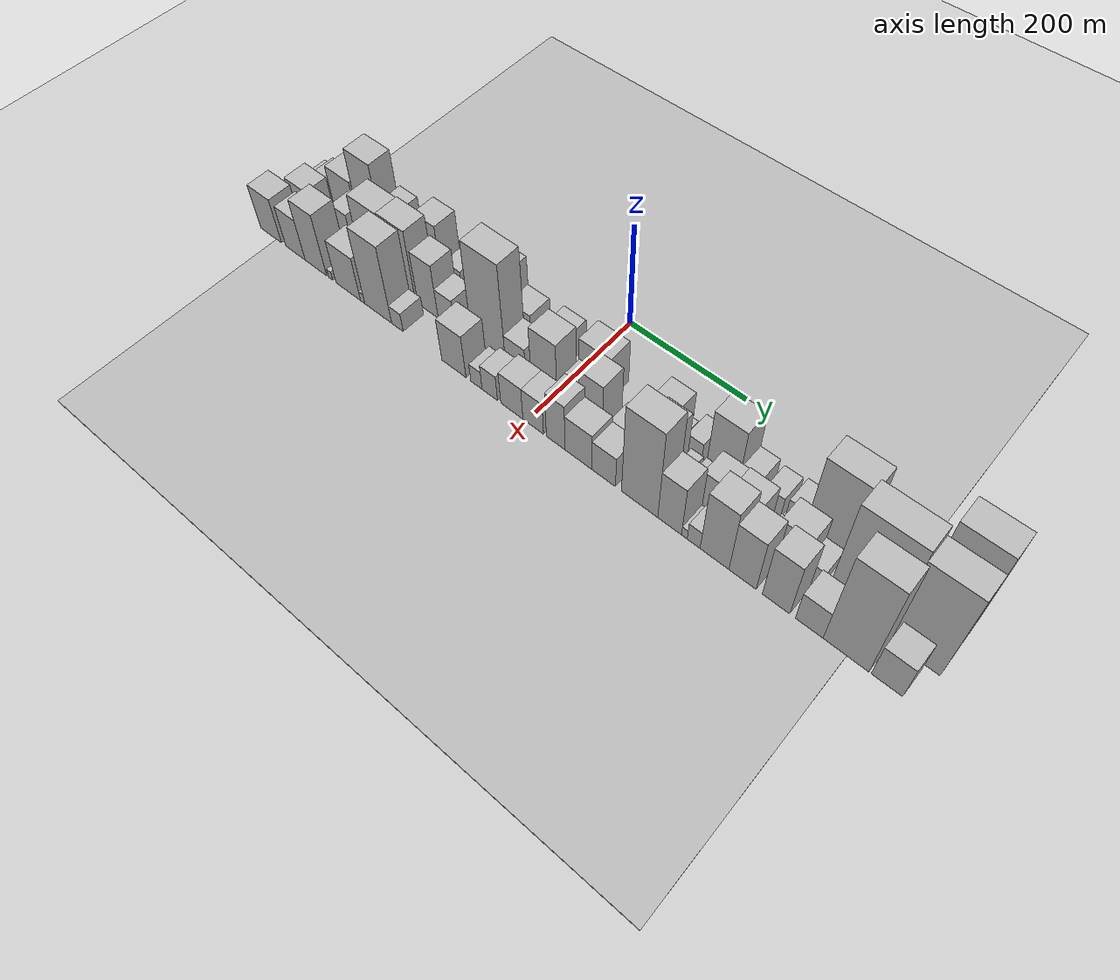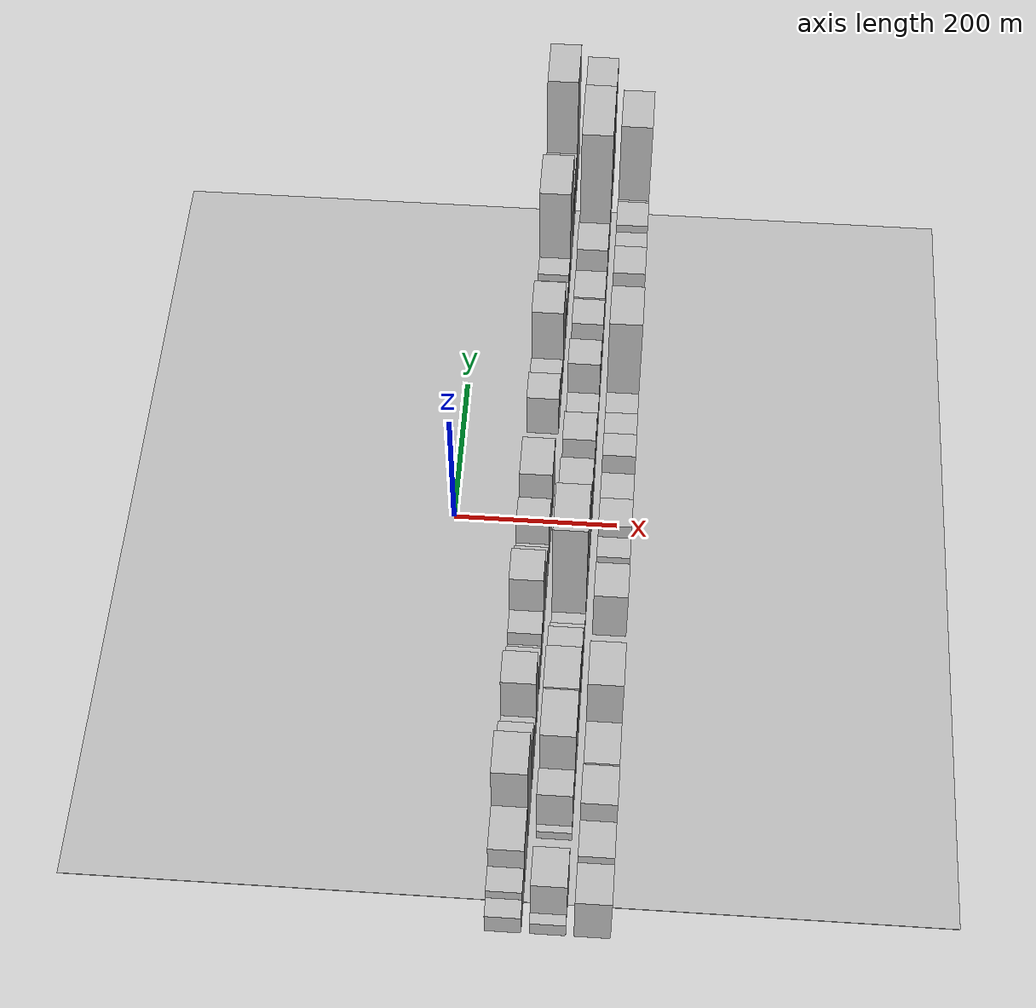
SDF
<?xml version="1.0" encoding="utf-8"?>

<sdf version="1.6">

   <world name="default">

      <gui fullscreen="0">

         <camera name="user_camera">

            <pose>-15 0 4.57585 0 0 0</pose>

            <view_controller>orbit</view_controller>

         </camera>

      </gui>

      <scene>

         <sky>

           <clouds>

             <speed>12</speed>

           </clouds>

         </sky>

         <ambient>0.4 0.4 0.4 1</ambient>

         <background>0.7 0.7 0.7 1</background>

         <shadows>1</shadows>

      </scene>

      <gravity>0 0 -9.8066</gravity>

      <magnetic_field>6e-06 2.3e-05 -4.2e-05</magnetic_field>

      <physics default="0" name="default_physics" type="ode">

         <ode>

            <solver>

               <type>quick</type>

               <iters>10</iters>

               <sor>1.0</sor>

               <use_dynamic_moi_rescaling>0</use_dynamic_moi_rescaling>

            </solver>

            <constraints>

               <cfm>0</cfm>

               <erp>0.2</erp>

               <contact_max_correcting_vel>100</contact_max_correcting_vel>

               <contact_surface_layer>0.001</contact_surface_layer>

            </constraints>

         </ode>

         <max_step_size>0.004</max_step_size>

         <real_time_factor>1</real_time_factor>

         <real_time_update_rate>250</real_time_update_rate>

      </physics>

      <light name="sun" type="directional">

         <cast_shadows>1</cast_shadows>

         <pose>0 0 10 0 0 0</pose>

         <diffuse>0.8 0.8 0.8 1</diffuse>

         <specular>0.2 0.2 0.2 1</specular>

         <attenuation>

            <range>1000</range>

            <constant>0.9</constant>

            <linear>0.01</linear>

            <quadratic>0.001</quadratic>

         </attenuation>

         <direction>-0.5 0.1 -0.9</direction>

      </light>

      <include>

         <name>ground_plane_1</name>

         <uri>model://HANNAS_ground_plane</uri>

         <pose>0 0 0  0 0 0</pose>

      </include>

      <include>

         <name>ground_plane_2</name>

         <uri>model://HANNAS_ground_plane</uri>

         <pose>100 0 0  0 0 0</pose>

      </include>

      <model name="building_1">

         <static>1</static>

         <pose frame="">100.0000 -525.0843 0 0.000000 0.000000 0.000000</pose>

         <link name="link">

            <pose frame="">0 0 19.50 0 0 0</pose>

            <collision name="collision">

               <geometry>

                  <box>

                     <size>40.0000 21.8315 39.0000</size>

                  </box>

               </geometry>

               <max_contacts>10</max_contacts>

               <surface>

                  <contact>

                     <ode/>

                  </contact>

                  <bounce/>

                  <friction>

                     <torsional>

                        <ode/>

                     </torsional>

                     <ode/>

                  </friction>

               </surface>

            </collision>

            <visual name="visual">

               <cast_shadows>0</cast_shadows>

               <geometry>

                  <box>

                     <size>40.0000 21.8315 39.0000</size>

                  </box>

               </geometry>

               <material>

                  <script>

                     <uri>model://HANNAS_wall/materials/scripts</uri>

                     <uri>model://HANNAS_wall/materials/textures</uri>

                     <name>vrc/HANNAS_wall</name>

                  </script>

               </material>

            </visual>

            <self_collide>0</self_collide>

            <enable_wind>0</enable_wind>

            <kinematic>0</kinematic>

         </link>

      </model>

      <model name="building_2">

         <static>1</static>

         <pose frame="">100.0000 -499.6968 0 0.000000 0.000000 0.000000</pose>

         <link name="link">

            <pose frame="">0 0 28.50 0 0 0</pose>

            <collision name="collision">

               <geometry>

                  <box>

                     <size>40.0000 28.9434 57.0000</size>

                  </box>

               </geometry>

               <max_contacts>10</max_contacts>

               <surface>

                  <contact>

                     <ode/>

                  </contact>

                  <bounce/>

                  <friction>

                     <torsional>

                        <ode/>

                     </torsional>

                     <ode/>

                  </friction>

               </surface>

            </collision>

            <visual name="visual">

               <cast_shadows>0</cast_shadows>

               <geometry>

                  <box>

                     <size>40.0000 28.9434 57.0000</size>

                  </box>

               </geometry>

               <material>

                  <script>

                     <uri>model://HANNAS_wall/materials/scripts</uri>

                     <uri>model://HANNAS_wall/materials/textures</uri>

                     <name>vrc/HANNAS_wall</name>

                  </script>

               </material>

            </visual>

            <self_collide>0</self_collide>

            <enable_wind>0</enable_wind>

            <kinematic>0</kinematic>

         </link>

      </model>

      <model name="building_3">

         <static>1</static>

         <pose frame="">100.0000 -454.3390 0 0.000000 0.000000 0.000000</pose>

         <link name="link">

            <pose frame="">0 0 45.00 0 0 0</pose>

            <collision name="collision">

               <geometry>

                  <box>

                     <size>40.0000 51.7723 90.0000</size>

                  </box>

               </geometry>

               <max_contacts>10</max_contacts>

               <surface>

                  <contact>

                     <ode/>

                  </contact>

                  <bounce/>

                  <friction>

                     <torsional>

                        <ode/>

                     </torsional>

                     <ode/>

                  </friction>

               </surface>

            </collision>

            <visual name="visual">

               <cast_shadows>0</cast_shadows>

               <geometry>

                  <box>

                     <size>40.0000 51.7723 90.0000</size>

                  </box>

               </geometry>

               <material>

                  <script>

                     <uri>model://HANNAS_wall/materials/scripts</uri>

                     <uri>model://HANNAS_wall/materials/textures</uri>

                     <name>vrc/HANNAS_wall</name>

                  </script>

               </material>

            </visual>

            <self_collide>0</self_collide>

            <enable_wind>0</enable_wind>

            <kinematic>0</kinematic>

         </link>

      </model>

      <model name="building_4">

         <static>1</static>

         <pose frame="">100.0000 -398.2001 0 0.000000 0.000000 0.000000</pose>

         <link name="link">

            <pose frame="">0 0 79.50 0 0 0</pose>

            <collision name="collision">

               <geometry>

                  <box>

                     <size>40.0000 50.5054 159.0000</size>

                  </box>

               </geometry>

               <max_contacts>10</max_contacts>

               <surface>

                  <contact>

                     <ode/>

                  </contact>

                  <bounce/>

                  <friction>

                     <torsional>

                        <ode/>

                     </torsional>

                     <ode/>

                  </friction>

               </surface>

            </collision>

            <visual name="visual">

               <cast_shadows>0</cast_shadows>

               <geometry>

                  <box>

                     <size>40.0000 50.5054 159.0000</size>

                  </box>

               </geometry>

               <material>

                  <script>

                     <uri>model://HANNAS_wall/materials/scripts</uri>

                     <uri>model://HANNAS_wall/materials/textures</uri>

                     <name>vrc/HANNAS_wall</name>

                  </script>

               </material>

            </visual>

            <self_collide>0</self_collide>

            <enable_wind>0</enable_wind>

            <kinematic>0</kinematic>

         </link>

      </model>

      <model name="building_5">

         <static>1</static>

         <pose frame="">100.0000 -345.5721 0 0.000000 0.000000 0.000000</pose>

         <link name="link">

            <pose frame="">0 0 48.00 0 0 0</pose>

            <collision name="collision">

               <geometry>

                  <box>

                     <size>40.0000 34.7506 96.0000</size>

                  </box>

               </geometry>

               <max_contacts>10</max_contacts>

               <surface>

                  <contact>

                     <ode/>

                  </contact>

                  <bounce/>

                  <friction>

                     <torsional>

                        <ode/>

                     </torsional>

                     <ode/>

                  </friction>

               </surface>

            </collision>

            <visual name="visual">

               <cast_shadows>0</cast_shadows>

               <geometry>

                  <box>

                     <size>40.0000 34.7506 96.0000</size>

                  </box>

               </geometry>

               <material>

                  <script>

                     <uri>model://HANNAS_wall/materials/scripts</uri>

                     <uri>model://HANNAS_wall/materials/textures</uri>

                     <name>vrc/HANNAS_wall</name>

                  </script>

               </material>

            </visual>

            <self_collide>0</self_collide>

            <enable_wind>0</enable_wind>

            <kinematic>0</kinematic>

         </link>

      </model>

      <model name="building_6">

         <static>1</static>

         <pose frame="">100.0000 -312.9346 0 0.000000 0.000000 0.000000</pose>

         <link name="link">

            <pose frame="">0 0 25.50 0 0 0</pose>

            <collision name="collision">

               <geometry>

                  <box>

                     <size>40.0000 30.5245 51.0000</size>

                  </box>

               </geometry>

               <max_contacts>10</max_contacts>

               <surface>

                  <contact>

                     <ode/>

                  </contact>

                  <bounce/>

                  <friction>

                     <torsional>

                        <ode/>

                     </torsional>

                     <ode/>

                  </friction>

               </surface>

            </collision>

            <visual name="visual">

               <cast_shadows>0</cast_shadows>

               <geometry>

                  <box>

                     <size>40.0000 30.5245 51.0000</size>

                  </box>

               </geometry>

               <material>

                  <script>

                     <uri>model://HANNAS_wall/materials/scripts</uri>

                     <uri>model://HANNAS_wall/materials/textures</uri>

                     <name>vrc/HANNAS_wall</name>

                  </script>

               </material>

            </visual>

            <self_collide>0</self_collide>

            <enable_wind>0</enable_wind>

            <kinematic>0</kinematic>

         </link>

      </model>

      <model name="building_7">

         <static>1</static>

         <pose frame="">100.0000 -272.1538 0 0.000000 0.000000 0.000000</pose>

         <link name="link">

            <pose frame="">0 0 60.00 0 0 0</pose>

            <collision name="collision">

               <geometry>

                  <box>

                     <size>40.0000 41.0372 120.0000</size>

                  </box>

               </geometry>

               <max_contacts>10</max_contacts>

               <surface>

                  <contact>

                     <ode/>

                  </contact>

                  <bounce/>

                  <friction>

                     <torsional>

                        <ode/>

                     </torsional>

                     <ode/>

                  </friction>

               </surface>

            </collision>

            <visual name="visual">

               <cast_shadows>0</cast_shadows>

               <geometry>

                  <box>

                     <size>40.0000 41.0372 120.0000</size>

                  </box>

               </geometry>

               <material>

                  <script>

                     <uri>model://HANNAS_wall/materials/scripts</uri>

                     <uri>model://HANNAS_wall/materials/textures</uri>

                     <name>vrc/HANNAS_wall</name>

                  </script>

               </material>

            </visual>

            <self_collide>0</self_collide>

            <enable_wind>0</enable_wind>

            <kinematic>0</kinematic>

         </link>

      </model>

      <model name="building_8">

         <static>1</static>

         <pose frame="">100.0000 -226.0152 0 0.000000 0.000000 0.000000</pose>

         <link name="link">

            <pose frame="">0 0 28.50 0 0 0</pose>

            <collision name="collision">

               <geometry>

                  <box>

                     <size>40.0000 31.2399 57.0000</size>

                  </box>

               </geometry>

               <max_contacts>10</max_contacts>

               <surface>

                  <contact>

                     <ode/>

                  </contact>

                  <bounce/>

                  <friction>

                     <torsional>

                        <ode/>

                     </torsional>

                     <ode/>

                  </friction>

               </surface>

            </collision>

            <visual name="visual">

               <cast_shadows>0</cast_shadows>

               <geometry>

                  <box>

                     <size>40.0000 31.2399 57.0000</size>

                  </box>

               </geometry>

               <material>

                  <script>

                     <uri>model://HANNAS_wall/materials/scripts</uri>

                     <uri>model://HANNAS_wall/materials/textures</uri>

                     <name>vrc/HANNAS_wall</name>

                  </script>

               </material>

            </visual>

            <self_collide>0</self_collide>

            <enable_wind>0</enable_wind>

            <kinematic>0</kinematic>

         </link>

      </model>

      <model name="building_9">

         <static>1</static>

         <pose frame="">100.0000 -196.6155 0 0.000000 0.000000 0.000000</pose>

         <link name="link">

            <pose frame="">0 0 13.50 0 0 0</pose>

            <collision name="collision">

               <geometry>

                  <box>

                     <size>40.0000 11.5596 27.0000</size>

                  </box>

               </geometry>

               <max_contacts>10</max_contacts>

               <surface>

                  <contact>

                     <ode/>

                  </contact>

                  <bounce/>

                  <friction>

                     <torsional>

                        <ode/>

                     </torsional>

                     <ode/>

                  </friction>

               </surface>

            </collision>

            <visual name="visual">

               <cast_shadows>0</cast_shadows>

               <geometry>

                  <box>

                     <size>40.0000 11.5596 27.0000</size>

                  </box>

               </geometry>

               <material>

                  <script>

                     <uri>model://HANNAS_wall/materials/scripts</uri>

                     <uri>model://HANNAS_wall/materials/textures</uri>

                     <name>vrc/HANNAS_wall</name>

                  </script>

               </material>

            </visual>

            <self_collide>0</self_collide>

            <enable_wind>0</enable_wind>

            <kinematic>0</kinematic>

         </link>

      </model>

      <model name="building_10">

         <static>1</static>

         <pose frame="">100.0000 -175.4859 0 0.000000 0.000000 0.000000</pose>

         <link name="link">

            <pose frame="">0 0 27.00 0 0 0</pose>

            <collision name="collision">

               <geometry>

                  <box>

                     <size>40.0000 30.6995 54.0000</size>

                  </box>

               </geometry>

               <max_contacts>10</max_contacts>

               <surface>

                  <contact>

                     <ode/>

                  </contact>

                  <bounce/>

                  <friction>

                     <torsional>

                        <ode/>

                     </torsional>

                     <ode/>

                  </friction>

               </surface>

            </collision>

            <visual name="visual">

               <cast_shadows>0</cast_shadows>

               <geometry>

                  <box>

                     <size>40.0000 30.6995 54.0000</size>

                  </box>

               </geometry>

               <material>

                  <script>

                     <uri>model://HANNAS_wall/materials/scripts</uri>

                     <uri>model://HANNAS_wall/materials/textures</uri>

                     <name>vrc/HANNAS_wall</name>

                  </script>

               </material>

            </visual>

            <self_collide>0</self_collide>

            <enable_wind>0</enable_wind>

            <kinematic>0</kinematic>

         </link>

      </model>

      <model name="building_11">

         <static>1</static>

         <pose frame="">100.0000 -139.2600 0 0.000000 0.000000 0.000000</pose>

         <link name="link">

            <pose frame="">0 0 61.50 0 0 0</pose>

            <collision name="collision">

               <geometry>

                  <box>

                     <size>40.0000 41.7524 123.0000</size>

                  </box>

               </geometry>

               <max_contacts>10</max_contacts>

               <surface>

                  <contact>

                     <ode/>

                  </contact>

                  <bounce/>

                  <friction>

                     <torsional>

                        <ode/>

                     </torsional>

                     <ode/>

                  </friction>

               </surface>

            </collision>

            <visual name="visual">

               <cast_shadows>0</cast_shadows>

               <geometry>

                  <box>

                     <size>40.0000 41.7524 123.0000</size>

                  </box>

               </geometry>

               <material>

                  <script>

                     <uri>model://HANNAS_wall/materials/scripts</uri>

                     <uri>model://HANNAS_wall/materials/textures</uri>

                     <name>vrc/HANNAS_wall</name>

                  </script>

               </material>

            </visual>

            <self_collide>0</self_collide>

            <enable_wind>0</enable_wind>

            <kinematic>0</kinematic>

         </link>

      </model>

      <model name="building_12">

         <static>1</static>

         <pose frame="">100.0000 -98.6339 0 0.000000 0.000000 0.000000</pose>

         <link name="link">

            <pose frame="">0 0 33.00 0 0 0</pose>

            <collision name="collision">

               <geometry>

                  <box>

                     <size>40.0000 39.4997 66.0000</size>

                  </box>

               </geometry>

               <max_contacts>10</max_contacts>

               <surface>

                  <contact>

                     <ode/>

                  </contact>

                  <bounce/>

                  <friction>

                     <torsional>

                        <ode/>

                     </torsional>

                     <ode/>

                  </friction>

               </surface>

            </collision>

            <visual name="visual">

               <cast_shadows>0</cast_shadows>

               <geometry>

                  <box>

                     <size>40.0000 39.4997 66.0000</size>

                  </box>

               </geometry>

               <material>

                  <script>

                     <uri>model://HANNAS_wall/materials/scripts</uri>

                     <uri>model://HANNAS_wall/materials/textures</uri>

                     <name>vrc/HANNAS_wall</name>

                  </script>

               </material>

            </visual>

            <self_collide>0</self_collide>

            <enable_wind>0</enable_wind>

            <kinematic>0</kinematic>

         </link>

      </model>

      <model name="building_13">

         <static>1</static>

         <pose frame="">100.0000 -74.4184 0 0.000000 0.000000 0.000000</pose>

         <link name="link">

            <pose frame="">0 0 10.50 0 0 0</pose>

            <collision name="collision">

               <geometry>

                  <box>

                     <size>40.0000 8.9314 21.0000</size>

                  </box>

               </geometry>

               <max_contacts>10</max_contacts>

               <surface>

                  <contact>

                     <ode/>

                  </contact>

                  <bounce/>

                  <friction>

                     <torsional>

                        <ode/>

                     </torsional>

                     <ode/>

                  </friction>

               </surface>

            </collision>

            <visual name="visual">

               <cast_shadows>0</cast_shadows>

               <geometry>

                  <box>

                     <size>40.0000 8.9314 21.0000</size>

                  </box>

               </geometry>

               <material>

                  <script>

                     <uri>model://HANNAS_wall/materials/scripts</uri>

                     <uri>model://HANNAS_wall/materials/textures</uri>

                     <name>vrc/HANNAS_wall</name>

                  </script>

               </material>

            </visual>

            <self_collide>0</self_collide>

            <enable_wind>0</enable_wind>

            <kinematic>0</kinematic>

         </link>

      </model>

      <model name="building_14">

         <static>1</static>

         <pose frame="">100.0000 -61.1851 0 0.000000 0.000000 0.000000</pose>

         <link name="link">

            <pose frame="">0 0 15.00 0 0 0</pose>

            <collision name="collision">

               <geometry>

                  <box>

                     <size>40.0000 17.5353 30.0000</size>

                  </box>

               </geometry>

               <max_contacts>10</max_contacts>

               <surface>

                  <contact>

                     <ode/>

                  </contact>

                  <bounce/>

                  <friction>

                     <torsional>

                        <ode/>

                     </torsional>

                     <ode/>

                  </friction>

               </surface>

            </collision>

            <visual name="visual">

               <cast_shadows>0</cast_shadows>

               <geometry>

                  <box>

                     <size>40.0000 17.5353 30.0000</size>

                  </box>

               </geometry>

               <material>

                  <script>

                     <uri>model://HANNAS_wall/materials/scripts</uri>

                     <uri>model://HANNAS_wall/materials/textures</uri>

                     <name>vrc/HANNAS_wall</name>

                  </script>

               </material>

            </visual>

            <self_collide>0</self_collide>

            <enable_wind>0</enable_wind>

            <kinematic>0</kinematic>

         </link>

      </model>

      <model name="building_15">

         <static>1</static>

         <pose frame="">100.0000 -33.0483 0 0.000000 0.000000 0.000000</pose>

         <link name="link">

            <pose frame="">0 0 36.00 0 0 0</pose>

            <collision name="collision">

               <geometry>

                  <box>

                     <size>40.0000 38.7382 72.0000</size>

                  </box>

               </geometry>

               <max_contacts>10</max_contacts>

               <surface>

                  <contact>

                     <ode/>

                  </contact>

                  <bounce/>

                  <friction>

                     <torsional>

                        <ode/>

                     </torsional>

                     <ode/>

                  </friction>

               </surface>

            </collision>

            <visual name="visual">

               <cast_shadows>0</cast_shadows>

               <geometry>

                  <box>

                     <size>40.0000 38.7382 72.0000</size>

                  </box>

               </geometry>

               <material>

                  <script>

                     <uri>model://HANNAS_wall/materials/scripts</uri>

                     <uri>model://HANNAS_wall/materials/textures</uri>

                     <name>vrc/HANNAS_wall</name>

                  </script>

               </material>

            </visual>

            <self_collide>0</self_collide>

            <enable_wind>0</enable_wind>

            <kinematic>0</kinematic>

         </link>

      </model>

      <model name="building_16">

         <static>1</static>

         <pose frame="">100.0000 -5.4757 0 0.000000 0.000000 0.000000</pose>

         <link name="link">

            <pose frame="">0 0 10.50 0 0 0</pose>

            <collision name="collision">

               <geometry>

                  <box>

                     <size>40.0000 8.4069 21.0000</size>

                  </box>

               </geometry>

               <max_contacts>10</max_contacts>

               <surface>

                  <contact>

                     <ode/>

                  </contact>

                  <bounce/>

                  <friction>

                     <torsional>

                        <ode/>

                     </torsional>

                     <ode/>

                  </friction>

               </surface>

            </collision>

            <visual name="visual">

               <cast_shadows>0</cast_shadows>

               <geometry>

                  <box>

                     <size>40.0000 8.4069 21.0000</size>

                  </box>

               </geometry>

               <material>

                  <script>

                     <uri>model://HANNAS_wall/materials/scripts</uri>

                     <uri>model://HANNAS_wall/materials/textures</uri>

                     <name>vrc/HANNAS_wall</name>

                  </script>

               </material>

            </visual>

            <self_collide>0</self_collide>

            <enable_wind>0</enable_wind>

            <kinematic>0</kinematic>

         </link>

      </model>

      <model name="building_17">

         <static>1</static>

         <pose frame="">100.0000 34.7056 0 0.000000 0.000000 0.000000</pose>

         <link name="link">

            <pose frame="">0 0 45.00 0 0 0</pose>

            <collision name="collision">

               <geometry>

                  <box>

                     <size>40.0000 53.9557 90.0000</size>

                  </box>

               </geometry>

               <max_contacts>10</max_contacts>

               <surface>

                  <contact>

                     <ode/>

                  </contact>

                  <bounce/>

                  <friction>

                     <torsional>

                        <ode/>

                     </torsional>

                     <ode/>

                  </friction>

               </surface>

            </collision>

            <visual name="visual">

               <cast_shadows>0</cast_shadows>

               <geometry>

                  <box>

                     <size>40.0000 53.9557 90.0000</size>

                  </box>

               </geometry>

               <material>

                  <script>

                     <uri>model://HANNAS_wall/materials/scripts</uri>

                     <uri>model://HANNAS_wall/materials/textures</uri>

                     <name>vrc/HANNAS_wall</name>

                  </script>

               </material>

            </visual>

            <self_collide>0</self_collide>

            <enable_wind>0</enable_wind>

            <kinematic>0</kinematic>

         </link>

      </model>

      <model name="building_18">

         <static>1</static>

         <pose frame="">100.0000 150.6203 0 0.000000 0.000000 0.000000</pose>

         <link name="link">

            <pose frame="">0 0 37.50 0 0 0</pose>

            <collision name="collision">

               <geometry>

                  <box>

                     <size>40.0000 39.2913 75.0000</size>

                  </box>

               </geometry>

               <max_contacts>10</max_contacts>

               <surface>

                  <contact>

                     <ode/>

                  </contact>

                  <bounce/>

                  <friction>

                     <torsional>

                        <ode/>

                     </torsional>

                     <ode/>

                  </friction>

               </surface>

            </collision>

            <visual name="visual">

               <cast_shadows>0</cast_shadows>

               <geometry>

                  <box>

                     <size>40.0000 39.2913 75.0000</size>

                  </box>

               </geometry>

               <material>

                  <script>

                     <uri>model://HANNAS_wall/materials/scripts</uri>

                     <uri>model://HANNAS_wall/materials/textures</uri>

                     <name>vrc/HANNAS_wall</name>

                  </script>

               </material>

            </visual>

            <self_collide>0</self_collide>

            <enable_wind>0</enable_wind>

            <kinematic>0</kinematic>

         </link>

      </model>

      <model name="building_19">

         <static>1</static>

         <pose frame="">100.0000 174.6894 0 0.000000 0.000000 0.000000</pose>

         <link name="link">

            <pose frame="">0 0 9.00 0 0 0</pose>

            <collision name="collision">

               <geometry>

                  <box>

                     <size>40.0000 8.8470 18.0000</size>

                  </box>

               </geometry>

               <max_contacts>10</max_contacts>

               <surface>

                  <contact>

                     <ode/>

                  </contact>

                  <bounce/>

                  <friction>

                     <torsional>

                        <ode/>

                     </torsional>

                     <ode/>

                  </friction>

               </surface>

            </collision>

            <visual name="visual">

               <cast_shadows>0</cast_shadows>

               <geometry>

                  <box>

                     <size>40.0000 8.8470 18.0000</size>

                  </box>

               </geometry>

               <material>

                  <script>

                     <uri>model://HANNAS_wall/materials/scripts</uri>

                     <uri>model://HANNAS_wall/materials/textures</uri>

                     <name>vrc/HANNAS_wall</name>

                  </script>

               </material>

            </visual>

            <self_collide>0</self_collide>

            <enable_wind>0</enable_wind>

            <kinematic>0</kinematic>

         </link>

      </model>

      <model name="building_20">

         <static>1</static>

         <pose frame="">100.0000 185.5754 0 0.000000 0.000000 0.000000</pose>

         <link name="link">

            <pose frame="">0 0 7.50 0 0 0</pose>

            <collision name="collision">

               <geometry>

                  <box>

                     <size>40.0000 6.9249 15.0000</size>

                  </box>

               </geometry>

               <max_contacts>10</max_contacts>

               <surface>

                  <contact>

                     <ode/>

                  </contact>

                  <bounce/>

                  <friction>

                     <torsional>

                        <ode/>

                     </torsional>

                     <ode/>

                  </friction>

               </surface>

            </collision>

            <visual name="visual">

               <cast_shadows>0</cast_shadows>

               <geometry>

                  <box>

                     <size>40.0000 6.9249 15.0000</size>

                  </box>

               </geometry>

               <material>

                  <script>

                     <uri>model://HANNAS_wall/materials/scripts</uri>

                     <uri>model://HANNAS_wall/materials/textures</uri>

                     <name>vrc/HANNAS_wall</name>

                  </script>

               </material>

            </visual>

            <self_collide>0</self_collide>

            <enable_wind>0</enable_wind>

            <kinematic>0</kinematic>

         </link>

      </model>

      <model name="building_21">

         <static>1</static>

         <pose frame="">100.0000 201.9347 0 0.000000 0.000000 0.000000</pose>

         <link name="link">

            <pose frame="">0 0 22.50 0 0 0</pose>

            <collision name="collision">

               <geometry>

                  <box>

                     <size>40.0000 25.7938 45.0000</size>

                  </box>

               </geometry>

               <max_contacts>10</max_contacts>

               <surface>

                  <contact>

                     <ode/>

                  </contact>

                  <bounce/>

                  <friction>

                     <torsional>

                        <ode/>

                     </torsional>

                     <ode/>

                  </friction>

               </surface>

            </collision>

            <visual name="visual">

               <cast_shadows>0</cast_shadows>

               <geometry>

                  <box>

                     <size>40.0000 25.7938 45.0000</size>

                  </box>

               </geometry>

               <material>

                  <script>

                     <uri>model://HANNAS_wall/materials/scripts</uri>

                     <uri>model://HANNAS_wall/materials/textures</uri>

                     <name>vrc/HANNAS_wall</name>

                  </script>

               </material>

            </visual>

            <self_collide>0</self_collide>

            <enable_wind>0</enable_wind>

            <kinematic>0</kinematic>

         </link>

      </model>

      <model name="building_22">

         <static>1</static>

         <pose frame="">100.0000 247.6585 0 0.000000 0.000000 0.000000</pose>

         <link name="link">

            <pose frame="">0 0 64.50 0 0 0</pose>

            <collision name="collision">

               <geometry>

                  <box>

                     <size>40.0000 49.6538 129.0000</size>

                  </box>

               </geometry>

               <max_contacts>10</max_contacts>

               <surface>

                  <contact>

                     <ode/>

                  </contact>

                  <bounce/>

                  <friction>

                     <torsional>

                        <ode/>

                     </torsional>

                     <ode/>

                  </friction>

               </surface>

            </collision>

            <visual name="visual">

               <cast_shadows>0</cast_shadows>

               <geometry>

                  <box>

                     <size>40.0000 49.6538 129.0000</size>

                  </box>

               </geometry>

               <material>

                  <script>

                     <uri>model://HANNAS_wall/materials/scripts</uri>

                     <uri>model://HANNAS_wall/materials/textures</uri>

                     <name>vrc/HANNAS_wall</name>

                  </script>

               </material>

            </visual>

            <self_collide>0</self_collide>

            <enable_wind>0</enable_wind>

            <kinematic>0</kinematic>

         </link>

      </model>

      <model name="building_23">

         <static>1</static>

         <pose frame="">100.0000 287.6734 0 0.000000 0.000000 0.000000</pose>

         <link name="link">

            <pose frame="">0 0 27.00 0 0 0</pose>

            <collision name="collision">

               <geometry>

                  <box>

                     <size>40.0000 30.3761 54.0000</size>

                  </box>

               </geometry>

               <max_contacts>10</max_contacts>

               <surface>

                  <contact>

                     <ode/>

                  </contact>

                  <bounce/>

                  <friction>

                     <torsional>

                        <ode/>

                     </torsional>

                     <ode/>

                  </friction>

               </surface>

            </collision>

            <visual name="visual">

               <cast_shadows>0</cast_shadows>

               <geometry>

                  <box>

                     <size>40.0000 30.3761 54.0000</size>

                  </box>

               </geometry>

               <material>

                  <script>

                     <uri>model://HANNAS_wall/materials/scripts</uri>

                     <uri>model://HANNAS_wall/materials/textures</uri>

                     <name>vrc/HANNAS_wall</name>

                  </script>

               </material>

            </visual>

            <self_collide>0</self_collide>

            <enable_wind>0</enable_wind>

            <kinematic>0</kinematic>

         </link>

      </model>

      <model name="building_24">

         <static>1</static>

         <pose frame="">100.0000 323.9697 0 0.000000 0.000000 0.000000</pose>

         <link name="link">

            <pose frame="">0 0 24.00 0 0 0</pose>

            <collision name="collision">

               <geometry>

                  <box>

                     <size>40.0000 28.2166 48.0000</size>

                  </box>

               </geometry>

               <max_contacts>10</max_contacts>

               <surface>

                  <contact>

                     <ode/>

                  </contact>

                  <bounce/>

                  <friction>

                     <torsional>

                        <ode/>

                     </torsional>

                     <ode/>

                  </friction>

               </surface>

            </collision>

            <visual name="visual">

               <cast_shadows>0</cast_shadows>

               <geometry>

                  <box>

                     <size>40.0000 28.2166 48.0000</size>

                  </box>

               </geometry>

               <material>

                  <script>

                     <uri>model://HANNAS_wall/materials/scripts</uri>

                     <uri>model://HANNAS_wall/materials/textures</uri>

                     <name>vrc/HANNAS_wall</name>

                  </script>

               </material>

            </visual>

            <self_collide>0</self_collide>

            <enable_wind>0</enable_wind>

            <kinematic>0</kinematic>

         </link>

      </model>

      <model name="building_25">

         <static>1</static>

         <pose frame="">100.0000 358.1570 0 0.000000 0.000000 0.000000</pose>

         <link name="link">

            <pose frame="">0 0 27.00 0 0 0</pose>

            <collision name="collision">

               <geometry>

                  <box>

                     <size>40.0000 28.1580 54.0000</size>

                  </box>

               </geometry>

               <max_contacts>10</max_contacts>

               <surface>

                  <contact>

                     <ode/>

                  </contact>

                  <bounce/>

                  <friction>

                     <torsional>

                        <ode/>

                     </torsional>

                     <ode/>

                  </friction>

               </surface>

            </collision>

            <visual name="visual">

               <cast_shadows>0</cast_shadows>

               <geometry>

                  <box>

                     <size>40.0000 28.1580 54.0000</size>

                  </box>

               </geometry>

               <material>

                  <script>

                     <uri>model://HANNAS_wall/materials/scripts</uri>

                     <uri>model://HANNAS_wall/materials/textures</uri>

                     <name>vrc/HANNAS_wall</name>

                  </script>

               </material>

            </visual>

            <self_collide>0</self_collide>

            <enable_wind>0</enable_wind>

            <kinematic>0</kinematic>

         </link>

      </model>

      <model name="building_26">

         <static>1</static>

         <pose frame="">100.0000 405.0540 0 0.000000 0.000000 0.000000</pose>

         <link name="link">

            <pose frame="">0 0 90.00 0 0 0</pose>

            <collision name="collision">

               <geometry>

                  <box>

                     <size>40.0000 65.6360 180.0000</size>

                  </box>

               </geometry>

               <max_contacts>10</max_contacts>

               <surface>

                  <contact>

                     <ode/>

                  </contact>

                  <bounce/>

                  <friction>

                     <torsional>

                        <ode/>

                     </torsional>

                     <ode/>

                  </friction>

               </surface>

            </collision>

            <visual name="visual">

               <cast_shadows>0</cast_shadows>

               <geometry>

                  <box>

                     <size>40.0000 65.6360 180.0000</size>

                  </box>

               </geometry>

               <material>

                  <script>

                     <uri>model://HANNAS_wall/materials/scripts</uri>

                     <uri>model://HANNAS_wall/materials/textures</uri>

                     <name>vrc/HANNAS_wall</name>

                  </script>

               </material>

            </visual>

            <self_collide>0</self_collide>

            <enable_wind>0</enable_wind>

            <kinematic>0</kinematic>

         </link>

      </model>

      <model name="building_27">

         <static>1</static>

         <pose frame="">100.0000 459.5757 0 0.000000 0.000000 0.000000</pose>

         <link name="link">

            <pose frame="">0 0 37.50 0 0 0</pose>

            <collision name="collision">

               <geometry>

                  <box>

                     <size>40.0000 43.4074 75.0000</size>

                  </box>

               </geometry>

               <max_contacts>10</max_contacts>

               <surface>

                  <contact>

                     <ode/>

                  </contact>

                  <bounce/>

                  <friction>

                     <torsional>

                        <ode/>

                     </torsional>

                     <ode/>

                  </friction>

               </surface>

            </collision>

            <visual name="visual">

               <cast_shadows>0</cast_shadows>

               <geometry>

                  <box>

                     <size>40.0000 43.4074 75.0000</size>

                  </box>

               </geometry>

               <material>

                  <script>

                     <uri>model://HANNAS_wall/materials/scripts</uri>

                     <uri>model://HANNAS_wall/materials/textures</uri>

                     <name>vrc/HANNAS_wall</name>

                  </script>

               </material>

            </visual>

            <self_collide>0</self_collide>

            <enable_wind>0</enable_wind>

            <kinematic>0</kinematic>

         </link>

      </model>

      <model name="building_28">

         <static>1</static>

         <pose frame="">100.0000 498.7292 0 0.000000 0.000000 0.000000</pose>

         <link name="link">

            <pose frame="">0 0 48.00 0 0 0</pose>

            <collision name="collision">

               <geometry>

                  <box>

                     <size>40.0000 34.8997 96.0000</size>

                  </box>

               </geometry>

               <max_contacts>10</max_contacts>

               <surface>

                  <contact>

                     <ode/>

                  </contact>

                  <bounce/>

                  <friction>

                     <torsional>

                        <ode/>

                     </torsional>

                     <ode/>

                  </friction>

               </surface>

            </collision>

            <visual name="visual">

               <cast_shadows>0</cast_shadows>

               <geometry>

                  <box>

                     <size>40.0000 34.8997 96.0000</size>

                  </box>

               </geometry>

               <material>

                  <script>

                     <uri>model://HANNAS_wall/materials/scripts</uri>

                     <uri>model://HANNAS_wall/materials/textures</uri>

                     <name>vrc/HANNAS_wall</name>

                  </script>

               </material>

            </visual>

            <self_collide>0</self_collide>

            <enable_wind>0</enable_wind>

            <kinematic>0</kinematic>

         </link>

      </model>

      <model name="building_29">

         <static>1</static>

         <pose frame="">100.0000 521.9105 0 0.000000 0.000000 0.000000</pose>

         <link name="link">

            <pose frame="">0 0 12.00 0 0 0</pose>

            <collision name="collision">

               <geometry>

                  <box>

                     <size>40.0000 11.4629 24.0000</size>

                  </box>

               </geometry>

               <max_contacts>10</max_contacts>

               <surface>

                  <contact>

                     <ode/>

                  </contact>

                  <bounce/>

                  <friction>

                     <torsional>

                        <ode/>

                     </torsional>

                     <ode/>

                  </friction>

               </surface>

            </collision>

            <visual name="visual">

               <cast_shadows>0</cast_shadows>

               <geometry>

                  <box>

                     <size>40.0000 11.4629 24.0000</size>

                  </box>

               </geometry>

               <material>

                  <script>

                     <uri>model://HANNAS_wall/materials/scripts</uri>

                     <uri>model://HANNAS_wall/materials/textures</uri>

                     <name>vrc/HANNAS_wall</name>

                  </script>

               </material>

            </visual>

            <self_collide>0</self_collide>

            <enable_wind>0</enable_wind>

            <kinematic>0</kinematic>

         </link>

      </model>

      <model name="building_30">

         <static>1</static>

         <pose frame="">100.0000 560.9484 0 0.000000 0.000000 0.000000</pose>

         <link name="link">

            <pose frame="">0 0 109.50 0 0 0</pose>

            <collision name="collision">

               <geometry>

                  <box>

                     <size>40.0000 66.6127 219.0000</size>

                  </box>

               </geometry>

               <max_contacts>10</max_contacts>

               <surface>

                  <contact>

                     <ode/>

                  </contact>

                  <bounce/>

                  <friction>

                     <torsional>

                        <ode/>

                     </torsional>

                     <ode/>

                  </friction>

               </surface>

            </collision>

            <visual name="visual">

               <cast_shadows>0</cast_shadows>

               <geometry>

                  <box>

                     <size>40.0000 66.6127 219.0000</size>

                  </box>

               </geometry>

               <material>

                  <script>

                     <uri>model://HANNAS_wall/materials/scripts</uri>

                     <uri>model://HANNAS_wall/materials/textures</uri>

                     <name>vrc/HANNAS_wall</name>

                  </script>

               </material>

            </visual>

            <self_collide>0</self_collide>

            <enable_wind>0</enable_wind>

            <kinematic>0</kinematic>

         </link>

      </model>

      <model name="building_31">

         <static>1</static>

         <pose frame="">149.0000 -529.6401 0 0.000000 0.000000 0.000000</pose>

         <link name="link">

            <pose frame="">0 0 13.50 0 0 0</pose>

            <collision name="collision">

               <geometry>

                  <box>

                     <size>40.0000 12.7197 27.0000</size>

                  </box>

               </geometry>

               <max_contacts>10</max_contacts>

               <surface>

                  <contact>

                     <ode/>

                  </contact>

                  <bounce/>

                  <friction>

                     <torsional>

                        <ode/>

                     </torsional>

                     <ode/>

                  </friction>

               </surface>

            </collision>

            <visual name="visual">

               <cast_shadows>0</cast_shadows>

               <geometry>

                  <box>

                     <size>40.0000 12.7197 27.0000</size>

                  </box>

               </geometry>

               <material>

                  <script>

                     <uri>model://HANNAS_wall/materials/scripts</uri>

                     <uri>model://HANNAS_wall/materials/textures</uri>

                     <name>vrc/HANNAS_wall</name>

                  </script>

               </material>

            </visual>

            <self_collide>0</self_collide>

            <enable_wind>0</enable_wind>

            <kinematic>0</kinematic>

         </link>

      </model>

      <model name="building_32">

         <static>1</static>

         <pose frame="">149.0000 -492.2932 0 0.000000 0.000000 0.000000</pose>

         <link name="link">

            <pose frame="">0 0 40.50 0 0 0</pose>

            <collision name="collision">

               <geometry>

                  <box>

                     <size>40.0000 45.9741 81.0000</size>

                  </box>

               </geometry>

               <max_contacts>10</max_contacts>

               <surface>

                  <contact>

                     <ode/>

                  </contact>

                  <bounce/>

                  <friction>

                     <torsional>

                        <ode/>

                     </torsional>

                     <ode/>

                  </friction>

               </surface>

            </collision>

            <visual name="visual">

               <cast_shadows>0</cast_shadows>

               <geometry>

                  <box>

                     <size>40.0000 45.9741 81.0000</size>

                  </box>

               </geometry>

               <material>

                  <script>

                     <uri>model://HANNAS_wall/materials/scripts</uri>

                     <uri>model://HANNAS_wall/materials/textures</uri>

                     <name>vrc/HANNAS_wall</name>

                  </script>

               </material>

            </visual>

            <self_collide>0</self_collide>

            <enable_wind>0</enable_wind>

            <kinematic>0</kinematic>

         </link>

      </model>

      <model name="building_33">

         <static>1</static>

         <pose frame="">149.0000 -418.1673 0 0.000000 0.000000 0.000000</pose>

         <link name="link">

            <pose frame="">0 0 9.00 0 0 0</pose>

            <collision name="collision">

               <geometry>

                  <box>

                     <size>40.0000 8.7592 18.0000</size>

                  </box>

               </geometry>

               <max_contacts>10</max_contacts>

               <surface>

                  <contact>

                     <ode/>

                  </contact>

                  <bounce/>

                  <friction>

                     <torsional>

                        <ode/>

                     </torsional>

                     <ode/>

                  </friction>

               </surface>

            </collision>

            <visual name="visual">

               <cast_shadows>0</cast_shadows>

               <geometry>

                  <box>

                     <size>40.0000 8.7592 18.0000</size>

                  </box>

               </geometry>

               <material>

                  <script>

                     <uri>model://HANNAS_wall/materials/scripts</uri>

                     <uri>model://HANNAS_wall/materials/textures</uri>

                     <name>vrc/HANNAS_wall</name>

                  </script>

               </material>

            </visual>

            <self_collide>0</self_collide>

            <enable_wind>0</enable_wind>

            <kinematic>0</kinematic>

         </link>

      </model>

      <model name="building_34">

         <static>1</static>

         <pose frame="">149.0000 -397.6507 0 0.000000 0.000000 0.000000</pose>

         <link name="link">

            <pose frame="">0 0 46.50 0 0 0</pose>

            <collision name="collision">

               <geometry>

                  <box>

                     <size>40.0000 32.2739 93.0000</size>

                  </box>

               </geometry>

               <max_contacts>10</max_contacts>

               <surface>

                  <contact>

                     <ode/>

                  </contact>

                  <bounce/>

                  <friction>

                     <torsional>

                        <ode/>

                     </torsional>

                     <ode/>

                  </friction>

               </surface>

            </collision>

            <visual name="visual">

               <cast_shadows>0</cast_shadows>

               <geometry>

                  <box>

                     <size>40.0000 32.2739 93.0000</size>

                  </box>

               </geometry>

               <material>

                  <script>

                     <uri>model://HANNAS_wall/materials/scripts</uri>

                     <uri>model://HANNAS_wall/materials/textures</uri>

                     <name>vrc/HANNAS_wall</name>

                  </script>

               </material>

            </visual>

            <self_collide>0</self_collide>

            <enable_wind>0</enable_wind>

            <kinematic>0</kinematic>

         </link>

      </model>

      <model name="building_35">

         <static>1</static>

         <pose frame="">149.0000 -370.4899 0 0.000000 0.000000 0.000000</pose>

         <link name="link">

            <pose frame="">0 0 7.50 0 0 0</pose>

            <collision name="collision">

               <geometry>

                  <box>

                     <size>40.0000 6.0475 15.0000</size>

                  </box>

               </geometry>

               <max_contacts>10</max_contacts>

               <surface>

                  <contact>

                     <ode/>

                  </contact>

                  <bounce/>

                  <friction>

                     <torsional>

                        <ode/>

                     </torsional>

                     <ode/>

                  </friction>

               </surface>

            </collision>

            <visual name="visual">

               <cast_shadows>0</cast_shadows>

               <geometry>

                  <box>

                     <size>40.0000 6.0475 15.0000</size>

                  </box>

               </geometry>

               <material>

                  <script>

                     <uri>model://HANNAS_wall/materials/scripts</uri>

                     <uri>model://HANNAS_wall/materials/textures</uri>

                     <name>vrc/HANNAS_wall</name>

                  </script>

               </material>

            </visual>

            <self_collide>0</self_collide>

            <enable_wind>0</enable_wind>

            <kinematic>0</kinematic>

         </link>

      </model>

      <model name="building_36">

         <static>1</static>

         <pose frame="">149.0000 -338.6855 0 0.000000 0.000000 0.000000</pose>

         <link name="link">

            <pose frame="">0 0 72.00 0 0 0</pose>

            <collision name="collision">

               <geometry>

                  <box>

                     <size>40.0000 57.5614 144.0000</size>

                  </box>

               </geometry>

               <max_contacts>10</max_contacts>

               <surface>

                  <contact>

                     <ode/>

                  </contact>

                  <bounce/>

                  <friction>

                     <torsional>

                        <ode/>

                     </torsional>

                     <ode/>

                  </friction>

               </surface>

            </collision>

            <visual name="visual">

               <cast_shadows>0</cast_shadows>

               <geometry>

                  <box>

                     <size>40.0000 57.5614 144.0000</size>

                  </box>

               </geometry>

               <material>

                  <script>

                     <uri>model://HANNAS_wall/materials/scripts</uri>

                     <uri>model://HANNAS_wall/materials/textures</uri>

                     <name>vrc/HANNAS_wall</name>

                  </script>

               </material>

            </visual>

            <self_collide>0</self_collide>

            <enable_wind>0</enable_wind>

            <kinematic>0</kinematic>

         </link>

      </model>

      <model name="building_37">

         <static>1</static>

         <pose frame="">149.0000 -283.4376 0 0.000000 0.000000 0.000000</pose>

         <link name="link">

            <pose frame="">0 0 73.50 0 0 0</pose>

            <collision name="collision">

               <geometry>

                  <box>

                     <size>40.0000 52.9343 147.0000</size>

                  </box>

               </geometry>

               <max_contacts>10</max_contacts>

               <surface>

                  <contact>

                     <ode/>

                  </contact>

                  <bounce/>

                  <friction>

                     <torsional>

                        <ode/>

                     </torsional>

                     <ode/>

                  </friction>

               </surface>

            </collision>

            <visual name="visual">

               <cast_shadows>0</cast_shadows>

               <geometry>

                  <box>

                     <size>40.0000 52.9343 147.0000</size>

                  </box>

               </geometry>

               <material>

                  <script>

                     <uri>model://HANNAS_wall/materials/scripts</uri>

                     <uri>model://HANNAS_wall/materials/textures</uri>

                     <name>vrc/HANNAS_wall</name>

                  </script>

               </material>

            </visual>

            <self_collide>0</self_collide>

            <enable_wind>0</enable_wind>

            <kinematic>0</kinematic>

         </link>

      </model>

      <model name="building_38">

         <static>1</static>

         <pose frame="">149.0000 -231.8540 0 0.000000 0.000000 0.000000</pose>

         <link name="link">

            <pose frame="">0 0 55.50 0 0 0</pose>

            <collision name="collision">

               <geometry>

                  <box>

                     <size>40.0000 40.2330 111.0000</size>

                  </box>

               </geometry>

               <max_contacts>10</max_contacts>

               <surface>

                  <contact>

                     <ode/>

                  </contact>

                  <bounce/>

                  <friction>

                     <torsional>

                        <ode/>

                     </torsional>

                     <ode/>

                  </friction>

               </surface>

            </collision>

            <visual name="visual">

               <cast_shadows>0</cast_shadows>

               <geometry>

                  <box>

                     <size>40.0000 40.2330 111.0000</size>

                  </box>

               </geometry>

               <material>

                  <script>

                     <uri>model://HANNAS_wall/materials/scripts</uri>

                     <uri>model://HANNAS_wall/materials/textures</uri>

                     <name>vrc/HANNAS_wall</name>

                  </script>

               </material>

            </visual>

            <self_collide>0</self_collide>

            <enable_wind>0</enable_wind>

            <kinematic>0</kinematic>

         </link>

      </model>

      <model name="building_39">

         <static>1</static>

         <pose frame="">149.0000 -195.4384 0 0.000000 0.000000 0.000000</pose>

         <link name="link">

            <pose frame="">0 0 31.50 0 0 0</pose>

            <collision name="collision">

               <geometry>

                  <box>

                     <size>40.0000 32.5982 63.0000</size>

                  </box>

               </geometry>

               <max_contacts>10</max_contacts>

               <surface>

                  <contact>

                     <ode/>

                  </contact>

                  <bounce/>

                  <friction>

                     <torsional>

                        <ode/>

                     </torsional>

                     <ode/>

                  </friction>

               </surface>

            </collision>

            <visual name="visual">

               <cast_shadows>0</cast_shadows>

               <geometry>

                  <box>

                     <size>40.0000 32.5982 63.0000</size>

                  </box>

               </geometry>

               <material>

                  <script>

                     <uri>model://HANNAS_wall/materials/scripts</uri>

                     <uri>model://HANNAS_wall/materials/textures</uri>

                     <name>vrc/HANNAS_wall</name>

                  </script>

               </material>

            </visual>

            <self_collide>0</self_collide>

            <enable_wind>0</enable_wind>

            <kinematic>0</kinematic>

         </link>

      </model>

      <model name="building_40">

         <static>1</static>

         <pose frame="">149.0000 -174.6834 0 0.000000 0.000000 0.000000</pose>

         <link name="link">

            <pose frame="">0 0 10.50 0 0 0</pose>

            <collision name="collision">

               <geometry>

                  <box>

                     <size>40.0000 8.9119 21.0000</size>

                  </box>

               </geometry>

               <max_contacts>10</max_contacts>

               <surface>

                  <contact>

                     <ode/>

                  </contact>

                  <bounce/>

                  <friction>

                     <torsional>

                        <ode/>

                     </torsional>

                     <ode/>

                  </friction>

               </surface>

            </collision>

            <visual name="visual">

               <cast_shadows>0</cast_shadows>

               <geometry>

                  <box>

                     <size>40.0000 8.9119 21.0000</size>

                  </box>

               </geometry>

               <material>

                  <script>

                     <uri>model://HANNAS_wall/materials/scripts</uri>

                     <uri>model://HANNAS_wall/materials/textures</uri>

                     <name>vrc/HANNAS_wall</name>

                  </script>

               </material>

            </visual>

            <self_collide>0</self_collide>

            <enable_wind>0</enable_wind>

            <kinematic>0</kinematic>

         </link>

      </model>

      <model name="building_41">

         <static>1</static>

         <pose frame="">149.0000 -154.3316 0 0.000000 0.000000 0.000000</pose>

         <link name="link">

            <pose frame="">0 0 15.00 0 0 0</pose>

            <collision name="collision">

               <geometry>

                  <box>

                     <size>40.0000 17.7917 30.0000</size>

                  </box>

               </geometry>

               <max_contacts>10</max_contacts>

               <surface>

                  <contact>

                     <ode/>

                  </contact>

                  <bounce/>

                  <friction>

                     <torsional>

                        <ode/>

                     </torsional>

                     <ode/>

                  </friction>

               </surface>

            </collision>

            <visual name="visual">

               <cast_shadows>0</cast_shadows>

               <geometry>

                  <box>

                     <size>40.0000 17.7917 30.0000</size>

                  </box>

               </geometry>

               <material>

                  <script>

                     <uri>model://HANNAS_wall/materials/scripts</uri>

                     <uri>model://HANNAS_wall/materials/textures</uri>

                     <name>vrc/HANNAS_wall</name>

                  </script>

               </material>

            </visual>

            <self_collide>0</self_collide>

            <enable_wind>0</enable_wind>

            <kinematic>0</kinematic>

         </link>

      </model>

      <model name="building_42">

         <static>1</static>

         <pose frame="">149.0000 -113.7942 0 0.000000 0.000000 0.000000</pose>

         <link name="link">

            <pose frame="">0 0 105.00 0 0 0</pose>

            <collision name="collision">

               <geometry>

                  <box>

                     <size>40.0000 63.2830 210.0000</size>

                  </box>

               </geometry>

               <max_contacts>10</max_contacts>

               <surface>

                  <contact>

                     <ode/>

                  </contact>

                  <bounce/>

                  <friction>

                     <torsional>

                        <ode/>

                     </torsional>

                     <ode/>

                  </friction>

               </surface>

            </collision>

            <visual name="visual">

               <cast_shadows>0</cast_shadows>

               <geometry>

                  <box>

                     <size>40.0000 63.2830 210.0000</size>

                  </box>

               </geometry>

               <material>

                  <script>

                     <uri>model://HANNAS_wall/materials/scripts</uri>

                     <uri>model://HANNAS_wall/materials/textures</uri>

                     <name>vrc/HANNAS_wall</name>

                  </script>

               </material>

            </visual>

            <self_collide>0</self_collide>

            <enable_wind>0</enable_wind>

            <kinematic>0</kinematic>

         </link>

      </model>

      <model name="building_43">

         <static>1</static>

         <pose frame="">149.0000 -63.5396 0 0.000000 0.000000 0.000000</pose>

         <link name="link">

            <pose frame="">0 0 34.50 0 0 0</pose>

            <collision name="collision">

               <geometry>

                  <box>

                     <size>40.0000 37.2262 69.0000</size>

                  </box>

               </geometry>

               <max_contacts>10</max_contacts>

               <surface>

                  <contact>

                     <ode/>

                  </contact>

                  <bounce/>

                  <friction>

                     <torsional>

                        <ode/>

                     </torsional>

                     <ode/>

                  </friction>

               </surface>

            </collision>

            <visual name="visual">

               <cast_shadows>0</cast_shadows>

               <geometry>

                  <box>

                     <size>40.0000 37.2262 69.0000</size>

                  </box>

               </geometry>

               <material>

                  <script>

                     <uri>model://HANNAS_wall/materials/scripts</uri>

                     <uri>model://HANNAS_wall/materials/textures</uri>

                     <name>vrc/HANNAS_wall</name>

                  </script>

               </material>

            </visual>

            <self_collide>0</self_collide>

            <enable_wind>0</enable_wind>

            <kinematic>0</kinematic>

         </link>

      </model>

      <model name="building_44">

         <static>1</static>

         <pose frame="">149.0000 -11.9843 0 0.000000 0.000000 0.000000</pose>

         <link name="link">

            <pose frame="">0 0 63.00 0 0 0</pose>

            <collision name="collision">

               <geometry>

                  <box>

                     <size>40.0000 45.8843 126.0000</size>

                  </box>

               </geometry>

               <max_contacts>10</max_contacts>

               <surface>

                  <contact>

                     <ode/>

                  </contact>

                  <bounce/>

                  <friction>

                     <torsional>

                        <ode/>

                     </torsional>

                     <ode/>

                  </friction>

               </surface>

            </collision>

            <visual name="visual">

               <cast_shadows>0</cast_shadows>

               <geometry>

                  <box>

                     <size>40.0000 45.8843 126.0000</size>

                  </box>

               </geometry>

               <material>

                  <script>

                     <uri>model://HANNAS_wall/materials/scripts</uri>

                     <uri>model://HANNAS_wall/materials/textures</uri>

                     <name>vrc/HANNAS_wall</name>

                  </script>

               </material>

            </visual>

            <self_collide>0</self_collide>

            <enable_wind>0</enable_wind>

            <kinematic>0</kinematic>

         </link>

      </model>

      <model name="building_45">

         <static>1</static>

         <pose frame="">149.0000 33.1688 0 0.000000 0.000000 0.000000</pose>

         <link name="link">

            <pose frame="">0 0 31.50 0 0 0</pose>

            <collision name="collision">

               <geometry>

                  <box>

                     <size>40.0000 32.4219 63.0000</size>

                  </box>

               </geometry>

               <max_contacts>10</max_contacts>

               <surface>

                  <contact>

                     <ode/>

                  </contact>

                  <bounce/>

                  <friction>

                     <torsional>

                        <ode/>

                     </torsional>

                     <ode/>

                  </friction>

               </surface>

            </collision>

            <visual name="visual">

               <cast_shadows>0</cast_shadows>

               <geometry>

                  <box>

                     <size>40.0000 32.4219 63.0000</size>

                  </box>

               </geometry>

               <material>

                  <script>

                     <uri>model://HANNAS_wall/materials/scripts</uri>

                     <uri>model://HANNAS_wall/materials/textures</uri>

                     <name>vrc/HANNAS_wall</name>

                  </script>

               </material>

            </visual>

            <self_collide>0</self_collide>

            <enable_wind>0</enable_wind>

            <kinematic>0</kinematic>

         </link>

      </model>

      <model name="building_46">

         <static>1</static>

         <pose frame="">149.0000 69.6636 0 0.000000 0.000000 0.000000</pose>

         <link name="link">

            <pose frame="">0 0 54.00 0 0 0</pose>

            <collision name="collision">

               <geometry>

                  <box>

                     <size>40.0000 40.5679 108.0000</size>

                  </box>

               </geometry>

               <max_contacts>10</max_contacts>

               <surface>

                  <contact>

                     <ode/>

                  </contact>

                  <bounce/>

                  <friction>

                     <torsional>

                        <ode/>

                     </torsional>

                     <ode/>

                  </friction>

               </surface>

            </collision>

            <visual name="visual">

               <cast_shadows>0</cast_shadows>

               <geometry>

                  <box>

                     <size>40.0000 40.5679 108.0000</size>

                  </box>

               </geometry>

               <material>

                  <script>

                     <uri>model://HANNAS_wall/materials/scripts</uri>

                     <uri>model://HANNAS_wall/materials/textures</uri>

                     <name>vrc/HANNAS_wall</name>

                  </script>

               </material>

            </visual>

            <self_collide>0</self_collide>

            <enable_wind>0</enable_wind>

            <kinematic>0</kinematic>

         </link>

      </model>

      <model name="building_47">

         <static>1</static>

         <pose frame="">149.0000 112.2504 0 0.000000 0.000000 0.000000</pose>

         <link name="link">

            <pose frame="">0 0 21.00 0 0 0</pose>

            <collision name="collision">

               <geometry>

                  <box>

                     <size>40.0000 24.6057 42.0000</size>

                  </box>

               </geometry>

               <max_contacts>10</max_contacts>

               <surface>

                  <contact>

                     <ode/>

                  </contact>

                  <bounce/>

                  <friction>

                     <torsional>

                        <ode/>

                     </torsional>

                     <ode/>

                  </friction>

               </surface>

            </collision>

            <visual name="visual">

               <cast_shadows>0</cast_shadows>

               <geometry>

                  <box>

                     <size>40.0000 24.6057 42.0000</size>

                  </box>

               </geometry>

               <material>

                  <script>

                     <uri>model://HANNAS_wall/materials/scripts</uri>

                     <uri>model://HANNAS_wall/materials/textures</uri>

                     <name>vrc/HANNAS_wall</name>

                  </script>

               </material>

            </visual>

            <self_collide>0</self_collide>

            <enable_wind>0</enable_wind>

            <kinematic>0</kinematic>

         </link>

      </model>

      <model name="building_48">

         <static>1</static>

         <pose frame="">149.0000 145.4254 0 0.000000 0.000000 0.000000</pose>

         <link name="link">

            <pose frame="">0 0 25.50 0 0 0</pose>

            <collision name="collision">

               <geometry>

                  <box>

                     <size>40.0000 29.7442 51.0000</size>

                  </box>

               </geometry>

               <max_contacts>10</max_contacts>

               <surface>

                  <contact>

                     <ode/>

                  </contact>

                  <bounce/>

                  <friction>

                     <torsional>

                        <ode/>

                     </torsional>

                     <ode/>

                  </friction>

               </surface>

            </collision>

            <visual name="visual">

               <cast_shadows>0</cast_shadows>

               <geometry>

                  <box>

                     <size>40.0000 29.7442 51.0000</size>

                  </box>

               </geometry>

               <material>

                  <script>

                     <uri>model://HANNAS_wall/materials/scripts</uri>

                     <uri>model://HANNAS_wall/materials/textures</uri>

                     <name>vrc/HANNAS_wall</name>

                  </script>

               </material>

            </visual>

            <self_collide>0</self_collide>

            <enable_wind>0</enable_wind>

            <kinematic>0</kinematic>

         </link>

      </model>

      <model name="building_49">

         <static>1</static>

         <pose frame="">149.0000 179.5197 0 0.000000 0.000000 0.000000</pose>

         <link name="link">

            <pose frame="">0 0 55.50 0 0 0</pose>

            <collision name="collision">

               <geometry>

                  <box>

                     <size>40.0000 38.4443 111.0000</size>

                  </box>

               </geometry>

               <max_contacts>10</max_contacts>

               <surface>

                  <contact>

                     <ode/>

                  </contact>

                  <bounce/>

                  <friction>

                     <torsional>

                        <ode/>

                     </torsional>

                     <ode/>

                  </friction>

               </surface>

            </collision>

            <visual name="visual">

               <cast_shadows>0</cast_shadows>

               <geometry>

                  <box>

                     <size>40.0000 38.4443 111.0000</size>

                  </box>

               </geometry>

               <material>

                  <script>

                     <uri>model://HANNAS_wall/materials/scripts</uri>

                     <uri>model://HANNAS_wall/materials/textures</uri>

                     <name>vrc/HANNAS_wall</name>

                  </script>

               </material>

            </visual>

            <self_collide>0</self_collide>

            <enable_wind>0</enable_wind>

            <kinematic>0</kinematic>

         </link>

      </model>

      <model name="building_50">

         <static>1</static>

         <pose frame="">149.0000 212.6584 0 0.000000 0.000000 0.000000</pose>

         <link name="link">

            <pose frame="">0 0 18.00 0 0 0</pose>

            <collision name="collision">

               <geometry>

                  <box>

                     <size>40.0000 19.8331 36.0000</size>

                  </box>

               </geometry>

               <max_contacts>10</max_contacts>

               <surface>

                  <contact>

                     <ode/>

                  </contact>

                  <bounce/>

                  <friction>

                     <torsional>

                        <ode/>

                     </torsional>

                     <ode/>

                  </friction>

               </surface>

            </collision>

            <visual name="visual">

               <cast_shadows>0</cast_shadows>

               <geometry>

                  <box>

                     <size>40.0000 19.8331 36.0000</size>

                  </box>

               </geometry>

               <material>

                  <script>

                     <uri>model://HANNAS_wall/materials/scripts</uri>

                     <uri>model://HANNAS_wall/materials/textures</uri>

                     <name>vrc/HANNAS_wall</name>

                  </script>

               </material>

            </visual>

            <self_collide>0</self_collide>

            <enable_wind>0</enable_wind>

            <kinematic>0</kinematic>

         </link>

      </model>

      <model name="building_51">

         <static>1</static>

         <pose frame="">149.0000 237.3529 0 0.000000 0.000000 0.000000</pose>

         <link name="link">

            <pose frame="">0 0 19.50 0 0 0</pose>

            <collision name="collision">

               <geometry>

                  <box>

                     <size>40.0000 21.5558 39.0000</size>

                  </box>

               </geometry>

               <max_contacts>10</max_contacts>

               <surface>

                  <contact>

                     <ode/>

                  </contact>

                  <bounce/>

                  <friction>

                     <torsional>

                        <ode/>

                     </torsional>

                     <ode/>

                  </friction>

               </surface>

            </collision>

            <visual name="visual">

               <cast_shadows>0</cast_shadows>

               <geometry>

                  <box>

                     <size>40.0000 21.5558 39.0000</size>

                  </box>

               </geometry>

               <material>

                  <script>

                     <uri>model://HANNAS_wall/materials/scripts</uri>

                     <uri>model://HANNAS_wall/materials/textures</uri>

                     <name>vrc/HANNAS_wall</name>

                  </script>

               </material>

            </visual>

            <self_collide>0</self_collide>

            <enable_wind>0</enable_wind>

            <kinematic>0</kinematic>

         </link>

      </model>

      <model name="building_52">

         <static>1</static>

         <pose frame="">149.0000 268.0263 0 0.000000 0.000000 0.000000</pose>

         <link name="link">

            <pose frame="">0 0 39.00 0 0 0</pose>

            <collision name="collision">

               <geometry>

                  <box>

                     <size>40.0000 39.7911 78.0000</size>

                  </box>

               </geometry>

               <max_contacts>10</max_contacts>

               <surface>

                  <contact>

                     <ode/>

                  </contact>

                  <bounce/>

                  <friction>

                     <torsional>

                        <ode/>

                     </torsional>

                     <ode/>

                  </friction>

               </surface>

            </collision>

            <visual name="visual">

               <cast_shadows>0</cast_shadows>

               <geometry>

                  <box>

                     <size>40.0000 39.7911 78.0000</size>

                  </box>

               </geometry>

               <material>

                  <script>

                     <uri>model://HANNAS_wall/materials/scripts</uri>

                     <uri>model://HANNAS_wall/materials/textures</uri>

                     <name>vrc/HANNAS_wall</name>

                  </script>

               </material>

            </visual>

            <self_collide>0</self_collide>

            <enable_wind>0</enable_wind>

            <kinematic>0</kinematic>

         </link>

      </model>

      <model name="building_53">

         <static>1</static>

         <pose frame="">149.0000 309.9628 0 0.000000 0.000000 0.000000</pose>

         <link name="link">

            <pose frame="">0 0 40.50 0 0 0</pose>

            <collision name="collision">

               <geometry>

                  <box>

                     <size>40.0000 44.0819 81.0000</size>

                  </box>

               </geometry>

               <max_contacts>10</max_contacts>

               <surface>

                  <contact>

                     <ode/>

                  </contact>

                  <bounce/>

                  <friction>

                     <torsional>

                        <ode/>

                     </torsional>

                     <ode/>

                  </friction>

               </surface>

            </collision>

            <visual name="visual">

               <cast_shadows>0</cast_shadows>

               <geometry>

                  <box>

                     <size>40.0000 44.0819 81.0000</size>

                  </box>

               </geometry>

               <material>

                  <script>

                     <uri>model://HANNAS_wall/materials/scripts</uri>

                     <uri>model://HANNAS_wall/materials/textures</uri>

                     <name>vrc/HANNAS_wall</name>

                  </script>

               </material>

            </visual>

            <self_collide>0</self_collide>

            <enable_wind>0</enable_wind>

            <kinematic>0</kinematic>

         </link>

      </model>

      <model name="building_54">

         <static>1</static>

         <pose frame="">149.0000 350.5146 0 0.000000 0.000000 0.000000</pose>

         <link name="link">

            <pose frame="">0 0 15.00 0 0 0</pose>

            <collision name="collision">

               <geometry>

                  <box>

                     <size>40.0000 17.0216 30.0000</size>

                  </box>

               </geometry>

               <max_contacts>10</max_contacts>

               <surface>

                  <contact>

                     <ode/>

                  </contact>

                  <bounce/>

                  <friction>

                     <torsional>

                        <ode/>

                     </torsional>

                     <ode/>

                  </friction>

               </surface>

            </collision>

            <visual name="visual">

               <cast_shadows>0</cast_shadows>

               <geometry>

                  <box>

                     <size>40.0000 17.0216 30.0000</size>

                  </box>

               </geometry>

               <material>

                  <script>

                     <uri>model://HANNAS_wall/materials/scripts</uri>

                     <uri>model://HANNAS_wall/materials/textures</uri>

                     <name>vrc/HANNAS_wall</name>

                  </script>

               </material>

            </visual>

            <self_collide>0</self_collide>

            <enable_wind>0</enable_wind>

            <kinematic>0</kinematic>

         </link>

      </model>

      <model name="building_55">

         <static>1</static>

         <pose frame="">149.0000 381.6897 0 0.000000 0.000000 0.000000</pose>

         <link name="link">

            <pose frame="">0 0 45.00 0 0 0</pose>

            <collision name="collision">

               <geometry>

                  <box>

                     <size>40.0000 45.3287 90.0000</size>

                  </box>

               </geometry>

               <max_contacts>10</max_contacts>

               <surface>

                  <contact>

                     <ode/>

                  </contact>

                  <bounce/>

                  <friction>

                     <torsional>

                        <ode/>

                     </torsional>

                     <ode/>

                  </friction>

               </surface>

            </collision>

            <visual name="visual">

               <cast_shadows>0</cast_shadows>

               <geometry>

                  <box>

                     <size>40.0000 45.3287 90.0000</size>

                  </box>

               </geometry>

               <material>

                  <script>

                     <uri>model://HANNAS_wall/materials/scripts</uri>

                     <uri>model://HANNAS_wall/materials/textures</uri>

                     <name>vrc/HANNAS_wall</name>

                  </script>

               </material>

            </visual>

            <self_collide>0</self_collide>

            <enable_wind>0</enable_wind>

            <kinematic>0</kinematic>

         </link>

      </model>

      <model name="building_56">

         <static>1</static>

         <pose frame="">149.0000 417.6556 0 0.000000 0.000000 0.000000</pose>

         <link name="link">

            <pose frame="">0 0 22.50 0 0 0</pose>

            <collision name="collision">

               <geometry>

                  <box>

                     <size>40.0000 26.6030 45.0000</size>

                  </box>

               </geometry>

               <max_contacts>10</max_contacts>

               <surface>

                  <contact>

                     <ode/>

                  </contact>

                  <bounce/>

                  <friction>

                     <torsional>

                        <ode/>

                     </torsional>

                     <ode/>

                  </friction>

               </surface>

            </collision>

            <visual name="visual">

               <cast_shadows>0</cast_shadows>

               <geometry>

                  <box>

                     <size>40.0000 26.6030 45.0000</size>

                  </box>

               </geometry>

               <material>

                  <script>

                     <uri>model://HANNAS_wall/materials/scripts</uri>

                     <uri>model://HANNAS_wall/materials/textures</uri>

                     <name>vrc/HANNAS_wall</name>

                  </script>

               </material>

            </visual>

            <self_collide>0</self_collide>

            <enable_wind>0</enable_wind>

            <kinematic>0</kinematic>

         </link>

      </model>

      <model name="building_57">

         <static>1</static>

         <pose frame="">149.0000 434.9982 0 0.000000 0.000000 0.000000</pose>

         <link name="link">

            <pose frame="">0 0 9.00 0 0 0</pose>

            <collision name="collision">

               <geometry>

                  <box>

                     <size>40.0000 8.0822 18.0000</size>

                  </box>

               </geometry>

               <max_contacts>10</max_contacts>

               <surface>

                  <contact>

                     <ode/>

                  </contact>

                  <bounce/>

                  <friction>

                     <torsional>

                        <ode/>

                     </torsional>

                     <ode/>

                  </friction>

               </surface>

            </collision>

            <visual name="visual">

               <cast_shadows>0</cast_shadows>

               <geometry>

                  <box>

                     <size>40.0000 8.0822 18.0000</size>

                  </box>

               </geometry>

               <material>

                  <script>

                     <uri>model://HANNAS_wall/materials/scripts</uri>

                     <uri>model://HANNAS_wall/materials/textures</uri>

                     <name>vrc/HANNAS_wall</name>

                  </script>

               </material>

            </visual>

            <self_collide>0</self_collide>

            <enable_wind>0</enable_wind>

            <kinematic>0</kinematic>

         </link>

      </model>

      <model name="building_58">

         <static>1</static>

         <pose frame="">149.0000 481.8063 0 0.000000 0.000000 0.000000</pose>

         <link name="link">

            <pose frame="">0 0 109.50 0 0 0</pose>

            <collision name="collision">

               <geometry>

                  <box>

                     <size>40.0000 85.5340 219.0000</size>

                  </box>

               </geometry>

               <max_contacts>10</max_contacts>

               <surface>

                  <contact>

                     <ode/>

                  </contact>

                  <bounce/>

                  <friction>

                     <torsional>

                        <ode/>

                     </torsional>

                     <ode/>

                  </friction>

               </surface>

            </collision>

            <visual name="visual">

               <cast_shadows>0</cast_shadows>

               <geometry>

                  <box>

                     <size>40.0000 85.5340 219.0000</size>

                  </box>

               </geometry>

               <material>

                  <script>

                     <uri>model://HANNAS_wall/materials/scripts</uri>

                     <uri>model://HANNAS_wall/materials/textures</uri>

                     <name>vrc/HANNAS_wall</name>

                  </script>

               </material>

            </visual>

            <self_collide>0</self_collide>

            <enable_wind>0</enable_wind>

            <kinematic>0</kinematic>

         </link>

      </model>

      <model name="building_59">

         <static>1</static>

         <pose frame="">149.0000 559.4920 0 0.000000 0.000000 0.000000</pose>

         <link name="link">

            <pose frame="">0 0 99.00 0 0 0</pose>

            <collision name="collision">

               <geometry>

                  <box>

                     <size>40.0000 69.8373 198.0000</size>

                  </box>

               </geometry>

               <max_contacts>10</max_contacts>

               <surface>

                  <contact>

                     <ode/>

                  </contact>

                  <bounce/>

                  <friction>

                     <torsional>

                        <ode/>

                     </torsional>

                     <ode/>

                  </friction>

               </surface>

            </collision>

            <visual name="visual">

               <cast_shadows>0</cast_shadows>

               <geometry>

                  <box>

                     <size>40.0000 69.8373 198.0000</size>

                  </box>

               </geometry>

               <material>

                  <script>

                     <uri>model://HANNAS_wall/materials/scripts</uri>

                     <uri>model://HANNAS_wall/materials/textures</uri>

                     <name>vrc/HANNAS_wall</name>

                  </script>

               </material>

            </visual>

            <self_collide>0</self_collide>

            <enable_wind>0</enable_wind>

            <kinematic>0</kinematic>

         </link>

      </model>

      <model name="building_60">

         <static>1</static>

         <pose frame="">198.0000 -512.5850 0 0.000000 0.000000 0.000000</pose>

         <link name="link">

            <pose frame="">0 0 45.00 0 0 0</pose>

            <collision name="collision">

               <geometry>

                  <box>

                     <size>40.0000 46.8301 90.0000</size>

                  </box>

               </geometry>

               <max_contacts>10</max_contacts>

               <surface>

                  <contact>

                     <ode/>

                  </contact>

                  <bounce/>

                  <friction>

                     <torsional>

                        <ode/>

                     </torsional>

                     <ode/>

                  </friction>

               </surface>

            </collision>

            <visual name="visual">

               <cast_shadows>0</cast_shadows>

               <geometry>

                  <box>

                     <size>40.0000 46.8301 90.0000</size>

                  </box>

               </geometry>

               <material>

                  <script>

                     <uri>model://HANNAS_wall/materials/scripts</uri>

                     <uri>model://HANNAS_wall/materials/textures</uri>

                     <name>vrc/HANNAS_wall</name>

                  </script>

               </material>

            </visual>

            <self_collide>0</self_collide>

            <enable_wind>0</enable_wind>

            <kinematic>0</kinematic>

         </link>

      </model>

      <model name="building_61">

         <static>1</static>

         <pose frame="">198.0000 -457.9122 0 0.000000 0.000000 0.000000</pose>

         <link name="link">

            <pose frame="">0 0 42.00 0 0 0</pose>

            <collision name="collision">

               <geometry>

                  <box>

                     <size>40.0000 42.5155 84.0000</size>

                  </box>

               </geometry>

               <max_contacts>10</max_contacts>

               <surface>

                  <contact>

                     <ode/>

                  </contact>

                  <bounce/>

                  <friction>

                     <torsional>

                        <ode/>

                     </torsional>

                     <ode/>

                  </friction>

               </surface>

            </collision>

            <visual name="visual">

               <cast_shadows>0</cast_shadows>

               <geometry>

                  <box>

                     <size>40.0000 42.5155 84.0000</size>

                  </box>

               </geometry>

               <material>

                  <script>

                     <uri>model://HANNAS_wall/materials/scripts</uri>

                     <uri>model://HANNAS_wall/materials/textures</uri>

                     <name>vrc/HANNAS_wall</name>

                  </script>

               </material>

            </visual>

            <self_collide>0</self_collide>

            <enable_wind>0</enable_wind>

            <kinematic>0</kinematic>

         </link>

      </model>

      <model name="building_62">

         <static>1</static>

         <pose frame="">198.0000 -413.3801 0 0.000000 0.000000 0.000000</pose>

         <link name="link">

            <pose frame="">0 0 63.00 0 0 0</pose>

            <collision name="collision">

               <geometry>

                  <box>

                     <size>40.0000 46.5487 126.0000</size>

                  </box>

               </geometry>

               <max_contacts>10</max_contacts>

               <surface>

                  <contact>

                     <ode/>

                  </contact>

                  <bounce/>

                  <friction>

                     <torsional>

                        <ode/>

                     </torsional>

                     <ode/>

                  </friction>

               </surface>

            </collision>

            <visual name="visual">

               <cast_shadows>0</cast_shadows>

               <geometry>

                  <box>

                     <size>40.0000 46.5487 126.0000</size>

                  </box>

               </geometry>

               <material>

                  <script>

                     <uri>model://HANNAS_wall/materials/scripts</uri>

                     <uri>model://HANNAS_wall/materials/textures</uri>

                     <name>vrc/HANNAS_wall</name>

                  </script>

               </material>

            </visual>

            <self_collide>0</self_collide>

            <enable_wind>0</enable_wind>

            <kinematic>0</kinematic>

         </link>

      </model>

      <model name="building_63">

         <static>1</static>

         <pose frame="">198.0000 -381.6772 0 0.000000 0.000000 0.000000</pose>

         <link name="link">

            <pose frame="">0 0 9.00 0 0 0</pose>

            <collision name="collision">

               <geometry>

                  <box>

                     <size>40.0000 8.8570 18.0000</size>

                  </box>

               </geometry>

               <max_contacts>10</max_contacts>

               <surface>

                  <contact>

                     <ode/>

                  </contact>

                  <bounce/>

                  <friction>

                     <torsional>

                        <ode/>

                     </torsional>

                     <ode/>

                  </friction>

               </surface>

            </collision>

            <visual name="visual">

               <cast_shadows>0</cast_shadows>

               <geometry>

                  <box>

                     <size>40.0000 8.8570 18.0000</size>

                  </box>

               </geometry>

               <material>

                  <script>

                     <uri>model://HANNAS_wall/materials/scripts</uri>

                     <uri>model://HANNAS_wall/materials/textures</uri>

                     <name>vrc/HANNAS_wall</name>

                  </script>

               </material>

            </visual>

            <self_collide>0</self_collide>

            <enable_wind>0</enable_wind>

            <kinematic>0</kinematic>

         </link>

      </model>

      <model name="building_64">

         <static>1</static>

         <pose frame="">198.0000 -344.4122 0 0.000000 0.000000 0.000000</pose>

         <link name="link">

            <pose frame="">0 0 45.00 0 0 0</pose>

            <collision name="collision">

               <geometry>

                  <box>

                     <size>40.0000 51.6730 90.0000</size>

                  </box>

               </geometry>

               <max_contacts>10</max_contacts>

               <surface>

                  <contact>

                     <ode/>

                  </contact>

                  <bounce/>

                  <friction>

                     <torsional>

                        <ode/>

                     </torsional>

                     <ode/>

                  </friction>

               </surface>

            </collision>

            <visual name="visual">

               <cast_shadows>0</cast_shadows>

               <geometry>

                  <box>

                     <size>40.0000 51.6730 90.0000</size>

                  </box>

               </geometry>

               <material>

                  <script>

                     <uri>model://HANNAS_wall/materials/scripts</uri>

                     <uri>model://HANNAS_wall/materials/textures</uri>

                     <name>vrc/HANNAS_wall</name>

                  </script>

               </material>

            </visual>

            <self_collide>0</self_collide>

            <enable_wind>0</enable_wind>

            <kinematic>0</kinematic>

         </link>

      </model>

      <model name="building_65">

         <static>1</static>

         <pose frame="">198.0000 -314.1652 0 0.000000 0.000000 0.000000</pose>

         <link name="link">

            <pose frame="">0 0 10.50 0 0 0</pose>

            <collision name="collision">

               <geometry>

                  <box>

                     <size>40.0000 8.8211 21.0000</size>

                  </box>

               </geometry>

               <max_contacts>10</max_contacts>

               <surface>

                  <contact>

                     <ode/>

                  </contact>

                  <bounce/>

                  <friction>

                     <torsional>

                        <ode/>

                     </torsional>

                     <ode/>

                  </friction>

               </surface>

            </collision>

            <visual name="visual">

               <cast_shadows>0</cast_shadows>

               <geometry>

                  <box>

                     <size>40.0000 8.8211 21.0000</size>

                  </box>

               </geometry>

               <material>

                  <script>

                     <uri>model://HANNAS_wall/materials/scripts</uri>

                     <uri>model://HANNAS_wall/materials/textures</uri>

                     <name>vrc/HANNAS_wall</name>

                  </script>

               </material>

            </visual>

            <self_collide>0</self_collide>

            <enable_wind>0</enable_wind>

            <kinematic>0</kinematic>

         </link>

      </model>

      <model name="building_66">

         <static>1</static>

         <pose frame="">198.0000 -282.3831 0 0.000000 0.000000 0.000000</pose>

         <link name="link">

            <pose frame="">0 0 79.50 0 0 0</pose>

            <collision name="collision">

               <geometry>

                  <box>

                     <size>40.0000 54.7430 159.0000</size>

                  </box>

               </geometry>

               <max_contacts>10</max_contacts>

               <surface>

                  <contact>

                     <ode/>

                  </contact>

                  <bounce/>

                  <friction>

                     <torsional>

                        <ode/>

                     </torsional>

                     <ode/>

                  </friction>

               </surface>

            </collision>

            <visual name="visual">

               <cast_shadows>0</cast_shadows>

               <geometry>

                  <box>

                     <size>40.0000 54.7430 159.0000</size>

                  </box>

               </geometry>

               <material>

                  <script>

                     <uri>model://HANNAS_wall/materials/scripts</uri>

                     <uri>model://HANNAS_wall/materials/textures</uri>

                     <name>vrc/HANNAS_wall</name>

                  </script>

               </material>

            </visual>

            <self_collide>0</self_collide>

            <enable_wind>0</enable_wind>

            <kinematic>0</kinematic>

         </link>

      </model>

      <model name="building_67">

         <static>1</static>

         <pose frame="">198.0000 -243.4870 0 0.000000 0.000000 0.000000</pose>

         <link name="link">

            <pose frame="">0 0 19.50 0 0 0</pose>

            <collision name="collision">

               <geometry>

                  <box>

                     <size>40.0000 23.0492 39.0000</size>

                  </box>

               </geometry>

               <max_contacts>10</max_contacts>

               <surface>

                  <contact>

                     <ode/>

                  </contact>

                  <bounce/>

                  <friction>

                     <torsional>

                        <ode/>

                     </torsional>

                     <ode/>

                  </friction>

               </surface>

            </collision>

            <visual name="visual">

               <cast_shadows>0</cast_shadows>

               <geometry>

                  <box>

                     <size>40.0000 23.0492 39.0000</size>

                  </box>

               </geometry>

               <material>

                  <script>

                     <uri>model://HANNAS_wall/materials/scripts</uri>

                     <uri>model://HANNAS_wall/materials/textures</uri>

                     <name>vrc/HANNAS_wall</name>

                  </script>

               </material>

            </visual>

            <self_collide>0</self_collide>

            <enable_wind>0</enable_wind>

            <kinematic>0</kinematic>

         </link>

      </model>

      <model name="building_68">

         <static>1</static>

         <pose frame="">198.0000 -133.2604 0 0.000000 0.000000 0.000000</pose>

         <link name="link">

            <pose frame="">0 0 45.00 0 0 0</pose>

            <collision name="collision">

               <geometry>

                  <box>

                     <size>40.0000 45.8013 90.0000</size>

                  </box>

               </geometry>

               <max_contacts>10</max_contacts>

               <surface>

                  <contact>

                     <ode/>

                  </contact>

                  <bounce/>

                  <friction>

                     <torsional>

                        <ode/>

                     </torsional>

                     <ode/>

                  </friction>

               </surface>

            </collision>

            <visual name="visual">

               <cast_shadows>0</cast_shadows>

               <geometry>

                  <box>

                     <size>40.0000 45.8013 90.0000</size>

                  </box>

               </geometry>

               <material>

                  <script>

                     <uri>model://HANNAS_wall/materials/scripts</uri>

                     <uri>model://HANNAS_wall/materials/textures</uri>

                     <name>vrc/HANNAS_wall</name>

                  </script>

               </material>

            </visual>

            <self_collide>0</self_collide>

            <enable_wind>0</enable_wind>

            <kinematic>0</kinematic>

         </link>

      </model>

      <model name="building_69">

         <static>1</static>

         <pose frame="">198.0000 -90.8490 0 0.000000 0.000000 0.000000</pose>

         <link name="link">

            <pose frame="">0 0 19.50 0 0 0</pose>

            <collision name="collision">

               <geometry>

                  <box>

                     <size>40.0000 21.0214 39.0000</size>

                  </box>

               </geometry>

               <max_contacts>10</max_contacts>

               <surface>

                  <contact>

                     <ode/>

                  </contact>

                  <bounce/>

                  <friction>

                     <torsional>

                        <ode/>

                     </torsional>

                     <ode/>

                  </friction>

               </surface>

            </collision>

            <visual name="visual">

               <cast_shadows>0</cast_shadows>

               <geometry>

                  <box>

                     <size>40.0000 21.0214 39.0000</size>

                  </box>

               </geometry>

               <material>

                  <script>

                     <uri>model://HANNAS_wall/materials/scripts</uri>

                     <uri>model://HANNAS_wall/materials/textures</uri>

                     <name>vrc/HANNAS_wall</name>

                  </script>

               </material>

            </visual>

            <self_collide>0</self_collide>

            <enable_wind>0</enable_wind>

            <kinematic>0</kinematic>

         </link>

      </model>

      <model name="building_70">

         <static>1</static>

         <pose frame="">198.0000 -66.1796 0 0.000000 0.000000 0.000000</pose>

         <link name="link">

            <pose frame="">0 0 27.00 0 0 0</pose>

            <collision name="collision">

               <geometry>

                  <box>

                     <size>40.0000 28.3174 54.0000</size>

                  </box>

               </geometry>

               <max_contacts>10</max_contacts>

               <surface>

                  <contact>

                     <ode/>

                  </contact>

                  <bounce/>

                  <friction>

                     <torsional>

                        <ode/>

                     </torsional>

                     <ode/>

                  </friction>

               </surface>

            </collision>

            <visual name="visual">

               <cast_shadows>0</cast_shadows>

               <geometry>

                  <box>

                     <size>40.0000 28.3174 54.0000</size>

                  </box>

               </geometry>

               <material>

                  <script>

                     <uri>model://HANNAS_wall/materials/scripts</uri>

                     <uri>model://HANNAS_wall/materials/textures</uri>

                     <name>vrc/HANNAS_wall</name>

                  </script>

               </material>

            </visual>

            <self_collide>0</self_collide>

            <enable_wind>0</enable_wind>

            <kinematic>0</kinematic>

         </link>

      </model>

      <model name="building_71">

         <static>1</static>

         <pose frame="">198.0000 -26.1277 0 0.000000 0.000000 0.000000</pose>

         <link name="link">

            <pose frame="">0 0 34.50 0 0 0</pose>

            <collision name="collision">

               <geometry>

                  <box>

                     <size>40.0000 39.7863 69.0000</size>

                  </box>

               </geometry>

               <max_contacts>10</max_contacts>

               <surface>

                  <contact>

                     <ode/>

                  </contact>

                  <bounce/>

                  <friction>

                     <torsional>

                        <ode/>

                     </torsional>

                     <ode/>

                  </friction>

               </surface>

            </collision>

            <visual name="visual">

               <cast_shadows>0</cast_shadows>

               <geometry>

                  <box>

                     <size>40.0000 39.7863 69.0000</size>

                  </box>

               </geometry>

               <material>

                  <script>

                     <uri>model://HANNAS_wall/materials/scripts</uri>

                     <uri>model://HANNAS_wall/materials/textures</uri>

                     <name>vrc/HANNAS_wall</name>

                  </script>

               </material>

            </visual>

            <self_collide>0</self_collide>

            <enable_wind>0</enable_wind>

            <kinematic>0</kinematic>

         </link>

      </model>

      <model name="building_72">

         <static>1</static>

         <pose frame="">198.0000 12.0300 0 0.000000 0.000000 0.000000</pose>

         <link name="link">

            <pose frame="">0 0 34.50 0 0 0</pose>

            <collision name="collision">

               <geometry>

                  <box>

                     <size>40.0000 36.5291 69.0000</size>

                  </box>

               </geometry>

               <max_contacts>10</max_contacts>

               <surface>

                  <contact>

                     <ode/>

                  </contact>

                  <bounce/>

                  <friction>

                     <torsional>

                        <ode/>

                     </torsional>

                     <ode/>

                  </friction>

               </surface>

            </collision>

            <visual name="visual">

               <cast_shadows>0</cast_shadows>

               <geometry>

                  <box>

                     <size>40.0000 36.5291 69.0000</size>

                  </box>

               </geometry>

               <material>

                  <script>

                     <uri>model://HANNAS_wall/materials/scripts</uri>

                     <uri>model://HANNAS_wall/materials/textures</uri>

                     <name>vrc/HANNAS_wall</name>

                  </script>

               </material>

            </visual>

            <self_collide>0</self_collide>

            <enable_wind>0</enable_wind>

            <kinematic>0</kinematic>

         </link>

      </model>

      <model name="building_73">

         <static>1</static>

         <pose frame="">198.0000 51.5324 0 0.000000 0.000000 0.000000</pose>

         <link name="link">

            <pose frame="">0 0 49.50 0 0 0</pose>

            <collision name="collision">

               <geometry>

                  <box>

                     <size>40.0000 32.4758 99.0000</size>

                  </box>

               </geometry>

               <max_contacts>10</max_contacts>

               <surface>

                  <contact>

                     <ode/>

                  </contact>

                  <bounce/>

                  <friction>

                     <torsional>

                        <ode/>

                     </torsional>

                     <ode/>

                  </friction>

               </surface>

            </collision>

            <visual name="visual">

               <cast_shadows>0</cast_shadows>

               <geometry>

                  <box>

                     <size>40.0000 32.4758 99.0000</size>

                  </box>

               </geometry>

               <material>

                  <script>

                     <uri>model://HANNAS_wall/materials/scripts</uri>

                     <uri>model://HANNAS_wall/materials/textures</uri>

                     <name>vrc/HANNAS_wall</name>

                  </script>

               </material>

            </visual>

            <self_collide>0</self_collide>

            <enable_wind>0</enable_wind>

            <kinematic>0</kinematic>

         </link>

      </model>

      <model name="building_74">

         <static>1</static>

         <pose frame="">198.0000 90.5555 0 0.000000 0.000000 0.000000</pose>

         <link name="link">

            <pose frame="">0 0 39.00 0 0 0</pose>

            <collision name="collision">

               <geometry>

                  <box>

                     <size>40.0000 45.5702 78.0000</size>

                  </box>

               </geometry>

               <max_contacts>10</max_contacts>

               <surface>

                  <contact>

                     <ode/>

                  </contact>

                  <bounce/>

                  <friction>

                     <torsional>

                        <ode/>

                     </torsional>

                     <ode/>

                  </friction>

               </surface>

            </collision>

            <visual name="visual">

               <cast_shadows>0</cast_shadows>

               <geometry>

                  <box>

                     <size>40.0000 45.5702 78.0000</size>

                  </box>

               </geometry>

               <material>

                  <script>

                     <uri>model://HANNAS_wall/materials/scripts</uri>

                     <uri>model://HANNAS_wall/materials/textures</uri>

                     <name>vrc/HANNAS_wall</name>

                  </script>

               </material>

            </visual>

            <self_collide>0</self_collide>

            <enable_wind>0</enable_wind>

            <kinematic>0</kinematic>

         </link>

      </model>

      <model name="building_75">

         <static>1</static>

         <pose frame="">198.0000 132.9082 0 0.000000 0.000000 0.000000</pose>

         <link name="link">

            <pose frame="">0 0 33.00 0 0 0</pose>

            <collision name="collision">

               <geometry>

                  <box>

                     <size>40.0000 39.1352 66.0000</size>

                  </box>

               </geometry>

               <max_contacts>10</max_contacts>

               <surface>

                  <contact>

                     <ode/>

                  </contact>

                  <bounce/>

                  <friction>

                     <torsional>

                        <ode/>

                     </torsional>

                     <ode/>

                  </friction>

               </surface>

            </collision>

            <visual name="visual">

               <cast_shadows>0</cast_shadows>

               <geometry>

                  <box>

                     <size>40.0000 39.1352 66.0000</size>

                  </box>

               </geometry>

               <material>

                  <script>

                     <uri>model://HANNAS_wall/materials/scripts</uri>

                     <uri>model://HANNAS_wall/materials/textures</uri>

                     <name>vrc/HANNAS_wall</name>

                  </script>

               </material>

            </visual>

            <self_collide>0</self_collide>

            <enable_wind>0</enable_wind>

            <kinematic>0</kinematic>

         </link>

      </model>

      <model name="building_76">

         <static>1</static>

         <pose frame="">198.0000 191.7233 0 0.000000 0.000000 0.000000</pose>

         <link name="link">

            <pose frame="">0 0 96.00 0 0 0</pose>

            <collision name="collision">

               <geometry>

                  <box>

                     <size>40.0000 58.4951 192.0000</size>

                  </box>

               </geometry>

               <max_contacts>10</max_contacts>

               <surface>

                  <contact>

                     <ode/>

                  </contact>

                  <bounce/>

                  <friction>

                     <torsional>

                        <ode/>

                     </torsional>

                     <ode/>

                  </friction>

               </surface>

            </collision>

            <visual name="visual">

               <cast_shadows>0</cast_shadows>

               <geometry>

                  <box>

                     <size>40.0000 58.4951 192.0000</size>

                  </box>

               </geometry>

               <material>

                  <script>

                     <uri>model://HANNAS_wall/materials/scripts</uri>

                     <uri>model://HANNAS_wall/materials/textures</uri>

                     <name>vrc/HANNAS_wall</name>

                  </script>

               </material>

            </visual>

            <self_collide>0</self_collide>

            <enable_wind>0</enable_wind>

            <kinematic>0</kinematic>

         </link>

      </model>

      <model name="building_77">

         <static>1</static>

         <pose frame="">198.0000 239.6193 0 0.000000 0.000000 0.000000</pose>

         <link name="link">

            <pose frame="">0 0 54.00 0 0 0</pose>

            <collision name="collision">

               <geometry>

                  <box>

                     <size>40.0000 37.2970 108.0000</size>

                  </box>

               </geometry>

               <max_contacts>10</max_contacts>

               <surface>

                  <contact>

                     <ode/>

                  </contact>

                  <bounce/>

                  <friction>

                     <torsional>

                        <ode/>

                     </torsional>

                     <ode/>

                  </friction>

               </surface>

            </collision>

            <visual name="visual">

               <cast_shadows>0</cast_shadows>

               <geometry>

                  <box>

                     <size>40.0000 37.2970 108.0000</size>

                  </box>

               </geometry>

               <material>

                  <script>

                     <uri>model://HANNAS_wall/materials/scripts</uri>

                     <uri>model://HANNAS_wall/materials/textures</uri>

                     <name>vrc/HANNAS_wall</name>

                  </script>

               </material>

            </visual>

            <self_collide>0</self_collide>

            <enable_wind>0</enable_wind>

            <kinematic>0</kinematic>

         </link>

      </model>

      <model name="building_78">

         <static>1</static>

         <pose frame="">198.0000 262.7277 0 0.000000 0.000000 0.000000</pose>

         <link name="link">

            <pose frame="">0 0 10.50 0 0 0</pose>

            <collision name="collision">

               <geometry>

                  <box>

                     <size>40.0000 8.9198 21.0000</size>

                  </box>

               </geometry>

               <max_contacts>10</max_contacts>

               <surface>

                  <contact>

                     <ode/>

                  </contact>

                  <bounce/>

                  <friction>

                     <torsional>

                        <ode/>

                     </torsional>

                     <ode/>

                  </friction>

               </surface>

            </collision>

            <visual name="visual">

               <cast_shadows>0</cast_shadows>

               <geometry>

                  <box>

                     <size>40.0000 8.9198 21.0000</size>

                  </box>

               </geometry>

               <material>

                  <script>

                     <uri>model://HANNAS_wall/materials/scripts</uri>

                     <uri>model://HANNAS_wall/materials/textures</uri>

                     <name>vrc/HANNAS_wall</name>

                  </script>

               </material>

            </visual>

            <self_collide>0</self_collide>

            <enable_wind>0</enable_wind>

            <kinematic>0</kinematic>

         </link>

      </model>

      <model name="building_79">

         <static>1</static>

         <pose frame="">198.0000 277.1560 0 0.000000 0.000000 0.000000</pose>

         <link name="link">

            <pose frame="">0 0 19.50 0 0 0</pose>

            <collision name="collision">

               <geometry>

                  <box>

                     <size>40.0000 19.9367 39.0000</size>

                  </box>

               </geometry>

               <max_contacts>10</max_contacts>

               <surface>

                  <contact>

                     <ode/>

                  </contact>

                  <bounce/>

                  <friction>

                     <torsional>

                        <ode/>

                     </torsional>

                     <ode/>

                  </friction>

               </surface>

            </collision>

            <visual name="visual">

               <cast_shadows>0</cast_shadows>

               <geometry>

                  <box>

                     <size>40.0000 19.9367 39.0000</size>

                  </box>

               </geometry>

               <material>

                  <script>

                     <uri>model://HANNAS_wall/materials/scripts</uri>

                     <uri>model://HANNAS_wall/materials/textures</uri>

                     <name>vrc/HANNAS_wall</name>

                  </script>

               </material>

            </visual>

            <self_collide>0</self_collide>

            <enable_wind>0</enable_wind>

            <kinematic>0</kinematic>

         </link>

      </model>

      <model name="building_80">

         <static>1</static>

         <pose frame="">198.0000 309.0452 0 0.000000 0.000000 0.000000</pose>

         <link name="link">

            <pose frame="">0 0 67.50 0 0 0</pose>

            <collision name="collision">

               <geometry>

                  <box>

                     <size>40.0000 43.8416 135.0000</size>

                  </box>

               </geometry>

               <max_contacts>10</max_contacts>

               <surface>

                  <contact>

                     <ode/>

                  </contact>

                  <bounce/>

                  <friction>

                     <torsional>

                        <ode/>

                     </torsional>

                     <ode/>

                  </friction>

               </surface>

            </collision>

            <visual name="visual">

               <cast_shadows>0</cast_shadows>

               <geometry>

                  <box>

                     <size>40.0000 43.8416 135.0000</size>

                  </box>

               </geometry>

               <material>

                  <script>

                     <uri>model://HANNAS_wall/materials/scripts</uri>

                     <uri>model://HANNAS_wall/materials/textures</uri>

                     <name>vrc/HANNAS_wall</name>

                  </script>

               </material>

            </visual>

            <self_collide>0</self_collide>

            <enable_wind>0</enable_wind>

            <kinematic>0</kinematic>

         </link>

      </model>

      <model name="building_81">

         <static>1</static>

         <pose frame="">198.0000 351.1544 0 0.000000 0.000000 0.000000</pose>

         <link name="link">

            <pose frame="">0 0 57.00 0 0 0</pose>

            <collision name="collision">

               <geometry>

                  <box>

                     <size>40.0000 40.3768 114.0000</size>

                  </box>

               </geometry>

               <max_contacts>10</max_contacts>

               <surface>

                  <contact>

                     <ode/>

                  </contact>

                  <bounce/>

                  <friction>

                     <torsional>

                        <ode/>

                     </torsional>

                     <ode/>

                  </friction>

               </surface>

            </collision>

            <visual name="visual">

               <cast_shadows>0</cast_shadows>

               <geometry>

                  <box>

                     <size>40.0000 40.3768 114.0000</size>

                  </box>

               </geometry>

               <material>

                  <script>

                     <uri>model://HANNAS_wall/materials/scripts</uri>

                     <uri>model://HANNAS_wall/materials/textures</uri>

                     <name>vrc/HANNAS_wall</name>

                  </script>

               </material>

            </visual>

            <self_collide>0</self_collide>

            <enable_wind>0</enable_wind>

            <kinematic>0</kinematic>

         </link>

      </model>

      <model name="building_82">

         <static>1</static>

         <pose frame="">198.0000 400.1579 0 0.000000 0.000000 0.000000</pose>

         <link name="link">

            <pose frame="">0 0 58.50 0 0 0</pose>

            <collision name="collision">

               <geometry>

                  <box>

                     <size>40.0000 39.6303 117.0000</size>

                  </box>

               </geometry>

               <max_contacts>10</max_contacts>

               <surface>

                  <contact>

                     <ode/>

                  </contact>

                  <bounce/>

                  <friction>

                     <torsional>

                        <ode/>

                     </torsional>

                     <ode/>

                  </friction>

               </surface>

            </collision>

            <visual name="visual">

               <cast_shadows>0</cast_shadows>

               <geometry>

                  <box>

                     <size>40.0000 39.6303 117.0000</size>

                  </box>

               </geometry>

               <material>

                  <script>

                     <uri>model://HANNAS_wall/materials/scripts</uri>

                     <uri>model://HANNAS_wall/materials/textures</uri>

                     <name>vrc/HANNAS_wall</name>

                  </script>

               </material>

            </visual>

            <self_collide>0</self_collide>

            <enable_wind>0</enable_wind>

            <kinematic>0</kinematic>

         </link>

      </model>

      <model name="building_83">

         <static>1</static>

         <pose frame="">198.0000 447.4905 0 0.000000 0.000000 0.000000</pose>

         <link name="link">

            <pose frame="">0 0 33.00 0 0 0</pose>

            <collision name="collision">

               <geometry>

                  <box>

                     <size>40.0000 39.0348 66.0000</size>

                  </box>

               </geometry>

               <max_contacts>10</max_contacts>

               <surface>

                  <contact>

                     <ode/>

                  </contact>

                  <bounce/>

                  <friction>

                     <torsional>

                        <ode/>

                     </torsional>

                     <ode/>

                  </friction>

               </surface>

            </collision>

            <visual name="visual">

               <cast_shadows>0</cast_shadows>

               <geometry>

                  <box>

                     <size>40.0000 39.0348 66.0000</size>

                  </box>

               </geometry>

               <material>

                  <script>

                     <uri>model://HANNAS_wall/materials/scripts</uri>

                     <uri>model://HANNAS_wall/materials/textures</uri>

                     <name>vrc/HANNAS_wall</name>

                  </script>

               </material>

            </visual>

            <self_collide>0</self_collide>

            <enable_wind>0</enable_wind>

            <kinematic>0</kinematic>

         </link>

      </model>

      <model name="building_84">

         <static>1</static>

         <pose frame="">198.0000 498.4020 0 0.000000 0.000000 0.000000</pose>

         <link name="link">

            <pose frame="">0 0 103.50 0 0 0</pose>

            <collision name="collision">

               <geometry>

                  <box>

                     <size>40.0000 62.7882 207.0000</size>

                  </box>

               </geometry>

               <max_contacts>10</max_contacts>

               <surface>

                  <contact>

                     <ode/>

                  </contact>

                  <bounce/>

                  <friction>

                     <torsional>

                        <ode/>

                     </torsional>

                     <ode/>

                  </friction>

               </surface>

            </collision>

            <visual name="visual">

               <cast_shadows>0</cast_shadows>

               <geometry>

                  <box>

                     <size>40.0000 62.7882 207.0000</size>

                  </box>

               </geometry>

               <material>

                  <script>

                     <uri>model://HANNAS_wall/materials/scripts</uri>

                     <uri>model://HANNAS_wall/materials/textures</uri>

                     <name>vrc/HANNAS_wall</name>

                  </script>

               </material>

            </visual>

            <self_collide>0</self_collide>

            <enable_wind>0</enable_wind>

            <kinematic>0</kinematic>

         </link>

      </model>

      <model name="building_85">

         <static>1</static>

         <pose frame="">198.0000 553.7124 0 0.000000 0.000000 0.000000</pose>

         <link name="link">

            <pose frame="">0 0 37.50 0 0 0</pose>

            <collision name="collision">

               <geometry>

                  <box>

                     <size>40.0000 41.8326 75.0000</size>

                  </box>

               </geometry>

               <max_contacts>10</max_contacts>

               <surface>

                  <contact>

                     <ode/>

                  </contact>

                  <bounce/>

                  <friction>

                     <torsional>

                        <ode/>

                     </torsional>

                     <ode/>

                  </friction>

               </surface>

            </collision>

            <visual name="visual">

               <cast_shadows>0</cast_shadows>

               <geometry>

                  <box>

                     <size>40.0000 41.8326 75.0000</size>

                  </box>

               </geometry>

               <material>

                  <script>

                     <uri>model://HANNAS_wall/materials/scripts</uri>

                     <uri>model://HANNAS_wall/materials/textures</uri>

                     <name>vrc/HANNAS_wall</name>

                  </script>

               </material>

            </visual>

            <self_collide>0</self_collide>

            <enable_wind>0</enable_wind>

            <kinematic>0</kinematic>

         </link>

      </model>

   </world>

</sdf>

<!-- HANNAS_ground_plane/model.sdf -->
<sdf version="1.4">
<model name="HANNAS_ground_plane">
  <static>true</static>
    <link name="link">
      <collision name="collision">
        <geometry>
          <plane>
            <normal>0 0 1</normal>
            <size>1000 1000</size>
          </plane>
        </geometry>
        <surface>
          <friction>
            <ode>
              <mu>100</mu>
              <mu2>50</mu2>
            </ode>
          </friction>
        </surface>
      </collision>
      <visual name="visual">
        <cast_shadows>false</cast_shadows>
        <geometry>
          <plane>
            <normal>0 0 1</normal>
            <size>1000 1000</size>
          </plane>
        </geometry>
        <material>
          <script>
            <uri>model://HANNAS_ground_plane/materials/scripts/HANNAS_ground_plane.material</uri>
	    <uri>model://HANNAS_ground_plane/materials/textures</uri>
            <name>HANNASGroundPlane/Image</name>
          </script>
        </material>
      </visual>
    </link>
  </model>
</sdf>
